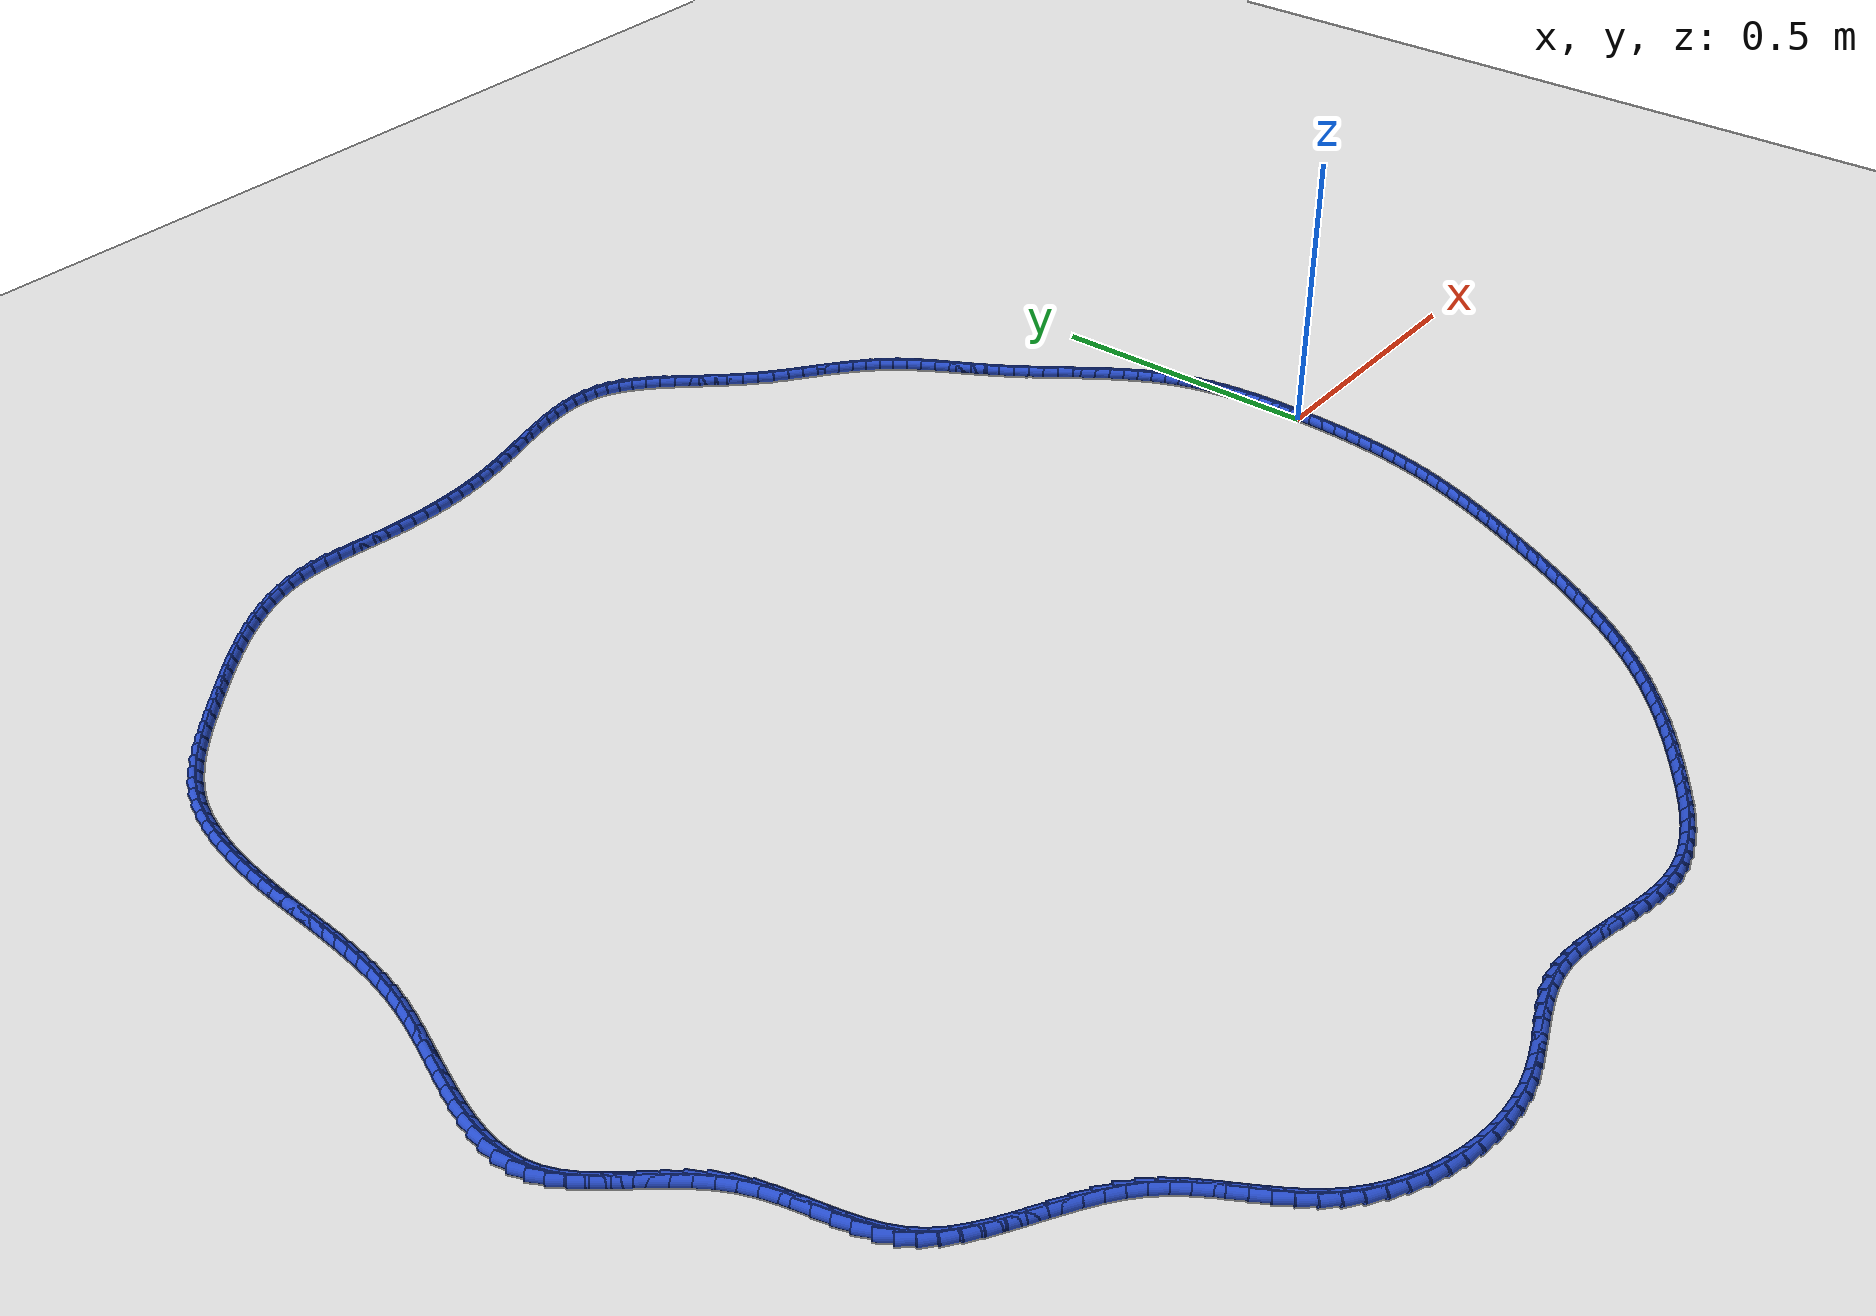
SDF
<sdf version="1.6">
 <world name="default">
  <light name="sun" type="directional">
   <pose>0 0 10 0 -0 0</pose>
   <diffuse>0.8 0.8 0.8 1</diffuse>
   <specular>0.2 0.2 0.2 1</specular>
   <attenuation>
    <range>1000</range>
    <constant>0.9</constant>
    <linear>0.01</linear>
    <quadratic>0.001</quadratic>
   </attenuation>
   <direction>-0.5 0.1 -0.9</direction>
  </light>
  <model name="ground_plane">
   <static>1</static>
   <link name="link">
    <collision name="collision">
     <geometry><plane><normal>0 0 1</normal><size>100 100</size></plane></geometry>
     <surface><friction><ode><mu>100</mu><mu2>50</mu2></ode></friction></surface>
    </collision>
    <visual name="visual">
     <cast_shadows>0</cast_shadows>
     <geometry><plane><normal>0 0 1</normal><size>100 100</size></plane></geometry>
     <material>
      <script><uri>file://media/materials/scripts/gazebo.material</uri><name>Gazebo/WhiteGlow</name></script>
     </material>
    </visual>
   </link>
  </model>
  <gravity>0 0 -9.8</gravity>
  <magnetic_field>6e-06 2.3e-05 -4.2e-05</magnetic_field>
  <atmosphere type="adiabatic"/>
  <physics name="default_physics" default="0" type="ode">
   <max_step_size>0.001</max_step_size>
   <real_time_factor>1</real_time_factor>
   <real_time_update_rate>1000</real_time_update_rate>
  </physics>
  <scene><ambient>0.4 0.4 0.4 1</ambient><background>0.7 0.7 0.7 1</background><shadows>1</shadows></scene>
  <spherical_coordinates>
   <surface_model>EARTH_WGS84</surface_model>
   <latitude_deg>0</latitude_deg>
   <longitude_deg>0</longitude_deg>
   <elevation>0</elevation>
   <heading_deg>0</heading_deg>
  </spherical_coordinates>
  <model name="line">
   <link name="link_0">
    <pose>6.288372600415926e-18 -5.551115123125783e-17 0.01 0 1.57 1.5576710177558442</pose>
    <collision name="collision">
     <geometry><cylinder><radius>0.01</radius><length>0.08</length></cylinder></geometry>
    </collision>
    <visual name="visual">
     <material>
      <script><name>Gazebo/Blue</name><uri>file://media/materials/scripts/gazebo.material</uri></script>
     </material>
     <geometry><cylinder><radius>0.01</radius><length>0.08</length></cylinder></geometry>
    </visual>
   </link>
   <link name="link_1">
    <pose>0.00035819239381342763 0.027288639335198456 0.01 0 1.57 -1.563014140440489</pose>
    <collision name="collision">
     <geometry><cylinder><radius>0.01</radius><length>0.08</length></cylinder></geometry>
    </collision>
    <visual name="visual">
     <material>
      <script><name>Gazebo/Blue</name><uri>file://media/materials/scripts/gazebo.material</uri></script>
     </material>
     <geometry><cylinder><radius>0.01</radius><length>0.08</length></cylinder></geometry>
    </visual>
   </link>
   <link name="link_2">
    <pose>0.0001455609213107466 0.05461093287966267 0.01 0 1.57 -1.5373915077967988</pose>
    <collision name="collision">
     <geometry><cylinder><radius>0.01</radius><length>0.08</length></cylinder></geometry>
    </collision>
    <visual name="visual">
     <material>
      <script><name>Gazebo/Blue</name><uri>file://media/materials/scripts/gazebo.material</uri></script>
     </material>
     <geometry><cylinder><radius>0.01</radius><length>0.08</length></cylinder></geometry>
    </visual>
   </link>
   <link name="link_3">
    <pose>-0.0007656347469176687 0.08187815783113758 0.01 0 1.57 -1.506824728913577</pose>
    <collision name="collision">
     <geometry><cylinder><radius>0.01</radius><length>0.08</length></cylinder></geometry>
    </collision>
    <visual name="visual">
     <material>
      <script><name>Gazebo/Blue</name><uri>file://media/materials/scripts/gazebo.material</uri></script>
     </material>
     <geometry><cylinder><radius>0.01</radius><length>0.08</length></cylinder></geometry>
    </visual>
   </link>
   <link name="link_4">
    <pose>-0.002503134940281458 0.10900159138736809 0.01 0 1.57 -1.4710373537824666</pose>
    <collision name="collision">
     <geometry><cylinder><radius>0.01</radius><length>0.08</length></cylinder></geometry>
    </collision>
    <visual name="visual">
     <material>
      <script><name>Gazebo/Blue</name><uri>file://media/materials/scripts/gazebo.material</uri></script>
     </material>
     <geometry><cylinder><radius>0.01</radius><length>0.08</length></cylinder></geometry>
    </visual>
   </link>
   <link name="link_5">
    <pose>-0.005194679988190256 0.13589251074609907 0.01 0 1.57 -1.42972331197012</pose>
    <collision name="collision">
     <geometry><cylinder><radius>0.01</radius><length>0.08</length></cylinder></geometry>
    </collision>
    <visual name="visual">
     <material>
      <script><name>Gazebo/Blue</name><uri>file://media/materials/scripts/gazebo.material</uri></script>
     </material>
     <geometry><cylinder><radius>0.01</radius><length>0.08</length></cylinder></geometry>
    </visual>
   </link>
   <link name="link_6">
    <pose>-0.008968010220053698 0.16246219310507543 0.01 0 1.57 -1.382572923634424</pose>
    <collision name="collision">
     <geometry><cylinder><radius>0.01</radius><length>0.08</length></cylinder></geometry>
    </collision>
    <visual name="visual">
     <material>
      <script><name>Gazebo/Blue</name><uri>file://media/materials/scripts/gazebo.material</uri></script>
     </material>
     <geometry><cylinder><radius>0.01</radius><length>0.08</length></cylinder></geometry>
    </visual>
   </link>
   <link name="link_7">
    <pose>-0.013950865965281417 0.18862191566204203 0.01 0 1.57 -1.329310111363557</pose>
    <collision name="collision">
     <geometry><cylinder><radius>0.01</radius><length>0.08</length></cylinder></geometry>
    </collision>
    <visual name="visual">
     <material>
      <script><name>Gazebo/Blue</name><uri>file://media/materials/scripts/gazebo.material</uri></script>
     </material>
     <geometry><cylinder><radius>0.01</radius><length>0.08</length></cylinder></geometry>
    </visual>
   </link>
   <link name="link_8">
    <pose>-0.020270987553283056 0.21428295561474392 0.01 0 1.57 -1.2697431346788266</pose>
    <collision name="collision">
     <geometry><cylinder><radius>0.01</radius><length>0.08</length></cylinder></geometry>
    </collision>
    <visual name="visual">
     <material>
      <script><name>Gazebo/Blue</name><uri>file://media/materials/scripts/gazebo.material</uri></script>
     </material>
     <geometry><cylinder><radius>0.01</radius><length>0.08</length></cylinder></geometry>
    </visual>
   </link>
   <link name="link_9">
    <pose>-0.028056115313468254 0.23935659016092592 0.01 0 1.57 -1.2043960556134092</pose>
    <collision name="collision">
     <geometry><cylinder><radius>0.01</radius><length>0.08</length></cylinder></geometry>
    </collision>
    <visual name="visual">
     <material>
      <script><name>Gazebo/Blue</name><uri>file://media/materials/scripts/gazebo.material</uri></script>
     </material>
     <geometry><cylinder><radius>0.01</radius><length>0.08</length></cylinder></geometry>
    </visual>
   </link>
   <link name="link_10">
    <pose>-0.03742097810335495 0.2637615625482717 0.01 0 1.57 -1.1413541810037235</pose>
    <collision name="collision">
     <geometry><cylinder><radius>0.01</radius><length>0.08</length></cylinder></geometry>
    </collision>
    <visual name="visual">
     <material>
      <script><name>Gazebo/Blue</name><uri>file://media/materials/scripts/gazebo.material</uri></script>
     </material>
     <geometry><cylinder><radius>0.01</radius><length>0.08</length></cylinder></geometry>
    </visual>
   </link>
   <link name="link_11">
    <pose>-0.048300866656210105 0.28751957854920734 0.01 0 1.57 -1.0868293325058338</pose>
    <collision name="collision">
     <geometry><cylinder><radius>0.01</radius><length>0.08</length></cylinder></geometry>
    </collision>
    <visual name="visual">
     <material>
      <script><name>Gazebo/Blue</name><uri>file://media/materials/scripts/gazebo.material</uri></script>
     </material>
     <geometry><cylinder><radius>0.01</radius><length>0.08</length></cylinder></geometry>
    </visual>
   </link>
   <link name="link_12">
    <pose>-0.06050034722363524 0.3107273543205694 0.01 0 1.57 -1.0412027712834304</pose>
    <collision name="collision">
     <geometry><cylinder><radius>0.01</radius><length>0.08</length></cylinder></geometry>
    </collision>
    <visual name="visual">
     <material>
      <script><name>Gazebo/Blue</name><uri>file://media/materials/scripts/gazebo.material</uri></script>
     </material>
     <geometry><cylinder><radius>0.01</radius><length>0.08</length></cylinder></geometry>
    </visual>
   </link>
   <link name="link_13">
    <pose>-0.07382102474752579 0.33348330523403574 0.01 0 1.57 -1.0044701815467032</pose>
    <collision name="collision">
     <geometry><cylinder><radius>0.01</radius><length>0.08</length></cylinder></geometry>
    </collision>
    <visual name="visual">
     <material>
      <script><name>Gazebo/Blue</name><uri>file://media/materials/scripts/gazebo.material</uri></script>
     </material>
     <geometry><cylinder><radius>0.01</radius><length>0.08</length></cylinder></geometry>
    </visual>
   </link>
   <link name="link_14">
    <pose>-0.08806450416977718 0.3558858466612842 0.01 0 1.57 -0.9764794870385074</pose>
    <collision name="collision">
     <geometry><cylinder><radius>0.01</radius><length>0.08</length></cylinder></geometry>
    </collision>
    <visual name="visual">
     <material>
      <script><name>Gazebo/Blue</name><uri>file://media/materials/scripts/gazebo.material</uri></script>
     </material>
     <geometry><cylinder><radius>0.01</radius><length>0.08</length></cylinder></geometry>
    </visual>
   </link>
   <link name="link_15">
    <pose>-0.10303239043228493 0.37803339397399294 0.01 0 1.57 -0.9570182973954346</pose>
    <collision name="collision">
     <geometry><cylinder><radius>0.01</radius><length>0.08</length></cylinder></geometry>
    </collision>
    <visual name="visual">
     <material>
      <script><name>Gazebo/Blue</name><uri>file://media/materials/scripts/gazebo.material</uri></script>
     </material>
     <geometry><cylinder><radius>0.01</radius><length>0.08</length></cylinder></geometry>
    </visual>
   </link>
   <link name="link_16">
    <pose>-0.11852628847694446 0.40002436254384 0.01 0 1.57 -0.9458761800640695</pose>
    <collision name="collision">
     <geometry><cylinder><radius>0.01</radius><length>0.08</length></cylinder></geometry>
    </collision>
    <visual name="visual">
     <material>
      <script><name>Gazebo/Blue</name><uri>file://media/materials/scripts/gazebo.material</uri></script>
     </material>
     <geometry><cylinder><radius>0.01</radius><length>0.08</length></cylinder></geometry>
    </visual>
   </link>
   <link name="link_17">
    <pose>-0.1343478032456513 0.4219571677425031 0.01 0 1.57 -0.9428837347033211</pose>
    <collision name="collision">
     <geometry><cylinder><radius>0.01</radius><length>0.08</length></cylinder></geometry>
    </collision>
    <visual name="visual">
     <material>
      <script><name>Gazebo/Blue</name><uri>file://media/materials/scripts/gazebo.material</uri></script>
     </material>
     <geometry><cylinder><radius>0.01</radius><length>0.08</length></cylinder></geometry>
    </visual>
   </link>
   <link name="link_18">
    <pose>-0.1502985396803008 0.4439302249416603 0.01 0 1.57 -0.9479322230216088</pose>
    <collision name="collision">
     <geometry><cylinder><radius>0.01</radius><length>0.08</length></cylinder></geometry>
    </collision>
    <visual name="visual">
     <material>
      <script><name>Gazebo/Blue</name><uri>file://media/materials/scripts/gazebo.material</uri></script>
     </material>
     <geometry><cylinder><radius>0.01</radius><length>0.08</length></cylinder></geometry>
    </visual>
   </link>
   <link name="link_19">
    <pose>-0.1661801027227884 0.46604194951298944 0.01 0 1.57 -0.9609769665578496</pose>
    <collision name="collision">
     <geometry><cylinder><radius>0.01</radius><length>0.08</length></cylinder></geometry>
    </collision>
    <visual name="visual">
     <material>
      <script><name>Gazebo/Blue</name><uri>file://media/materials/scripts/gazebo.material</uri></script>
     </material>
     <geometry><cylinder><radius>0.01</radius><length>0.08</length></cylinder></geometry>
    </visual>
   </link>
   <link name="link_20">
    <pose>-0.18179409731500973 0.4883907568281688 0.01 0 1.57 -0.9820262279820207</pose>
    <collision name="collision">
     <geometry><cylinder><radius>0.01</radius><length>0.08</length></cylinder></geometry>
    </collision>
    <visual name="visual">
     <material>
      <script><name>Gazebo/Blue</name><uri>file://media/materials/scripts/gazebo.material</uri></script>
     </material>
     <geometry><cylinder><radius>0.01</radius><length>0.08</length></cylinder></geometry>
    </visual>
   </link>
   <link name="link_21">
    <pose>-0.19694212839886005 0.5110750622588759 0.01 0 1.57 -1.0109300378586217</pose>
    <collision name="collision">
     <geometry><cylinder><radius>0.01</radius><length>0.08</length></cylinder></geometry>
    </collision>
    <visual name="visual">
     <material>
      <script><name>Gazebo/Blue</name><uri>file://media/materials/scripts/gazebo.material</uri></script>
     </material>
     <geometry><cylinder><radius>0.01</radius><length>0.08</length></cylinder></geometry>
    </visual>
   </link>
   <link name="link_22">
    <pose>-0.2114299420428363 0.5341903500423052 0.01 0 1.57 -1.039145391755223</pose>
    <collision name="collision">
     <geometry><cylinder><radius>0.01</radius><length>0.08</length></cylinder></geometry>
    </collision>
    <visual name="visual">
     <material>
      <script><name>Gazebo/Blue</name><uri>file://media/materials/scripts/gazebo.material</uri></script>
     </material>
     <geometry><cylinder><radius>0.01</radius><length>0.08</length></cylinder></geometry>
    </visual>
   </link>
   <link name="link_23">
    <pose>-0.22525480229039502 0.5576965459083251 0.01 0 1.57 -1.0547436627425568</pose>
    <collision name="collision">
     <geometry><cylinder><radius>0.01</radius><length>0.08</length></cylinder></geometry>
    </collision>
    <visual name="visual">
     <material>
      <script><name>Gazebo/Blue</name><uri>file://media/materials/scripts/gazebo.material</uri></script>
     </material>
     <geometry><cylinder><radius>0.01</radius><length>0.08</length></cylinder></geometry>
    </visual>
   </link>
   <link name="link_24">
    <pose>-0.23868202464836102 0.581363845843327 0.01 0 1.57 -1.056841591952224</pose>
    <collision name="collision">
     <geometry><cylinder><radius>0.01</radius><length>0.08</length></cylinder></geometry>
    </collision>
    <visual name="visual">
     <material>
      <script><name>Gazebo/Blue</name><uri>file://media/materials/scripts/gazebo.material</uri></script>
     </material>
     <geometry><cylinder><radius>0.01</radius><length>0.08</length></cylinder></geometry>
    </visual>
   </link>
   <link name="link_25">
    <pose>-0.25199691686086373 0.604948295110525 0.01 0 1.57 -1.0452628420765173</pose>
    <collision name="collision">
     <geometry><cylinder><radius>0.01</radius><length>0.08</length></cylinder></geometry>
    </collision>
    <visual name="visual">
     <material>
      <script><name>Gazebo/Blue</name><uri>file://media/materials/scripts/gazebo.material</uri></script>
     </material>
     <geometry><cylinder><radius>0.01</radius><length>0.08</length></cylinder></geometry>
    </visual>
   </link>
   <link name="link_26">
    <pose>-0.2654847866720326 0.6282059389731328 0.01 0 1.57 -1.0196211803375106</pose>
    <collision name="collision">
     <geometry><cylinder><radius>0.01</radius><length>0.08</length></cylinder></geometry>
    </collision>
    <visual name="visual">
     <material>
      <script><name>Gazebo/Blue</name><uri>file://media/materials/scripts/gazebo.material</uri></script>
     </material>
     <geometry><cylinder><radius>0.01</radius><length>0.08</length></cylinder></geometry>
    </visual>
   </link>
   <link name="link_27">
    <pose>-0.2794309418259971 0.6508928226943647 0.01 0 1.57 -0.9793735186141798</pose>
    <collision name="collision">
     <geometry><cylinder><radius>0.01</radius><length>0.08</length></cylinder></geometry>
    </collision>
    <visual name="visual">
     <material>
      <script><name>Gazebo/Blue</name><uri>file://media/materials/scripts/gazebo.material</uri></script>
     </material>
     <geometry><cylinder><radius>0.01</radius><length>0.08</length></cylinder></geometry>
    </visual>
   </link>
   <link name="link_28">
    <pose>-0.2941206900668865 0.6727649915374343 0.01 0 1.57 -0.9239665071199855</pose>
    <collision name="collision">
     <geometry><cylinder><radius>0.01</radius><length>0.08</length></cylinder></geometry>
    </collision>
    <visual name="visual">
     <material>
      <script><name>Gazebo/Blue</name><uri>file://media/materials/scripts/gazebo.material</uri></script>
     </material>
     <geometry><cylinder><radius>0.01</radius><length>0.08</length></cylinder></geometry>
    </visual>
   </link>
   <link name="link_29">
    <pose>-0.3098393391388304 0.6935784907655561 0.01 0 1.57 -0.8539680803957829</pose>
    <collision name="collision">
     <geometry><cylinder><radius>0.01</radius><length>0.08</length></cylinder></geometry>
    </collision>
    <visual name="visual">
     <material>
      <script><name>Gazebo/Blue</name><uri>file://media/materials/scripts/gazebo.material</uri></script>
     </material>
     <geometry><cylinder><radius>0.01</radius><length>0.08</length></cylinder></geometry>
    </visual>
   </link>
   <link name="link_30">
    <pose>-0.3268565889247437 0.7131055129945613 0.01 0 1.57 -0.7843573897227736</pose>
    <collision name="collision">
     <geometry><cylinder><radius>0.01</radius><length>0.08</length></cylinder></geometry>
    </collision>
    <visual name="visual">
     <material>
      <script><name>Gazebo/Blue</name><uri>file://media/materials/scripts/gazebo.material</uri></script>
     </material>
     <geometry><cylinder><radius>0.01</radius><length>0.08</length></cylinder></geometry>
    </visual>
   </link>
   <link name="link_31">
    <pose>-0.3451793251737625 0.7313901492402318 0.01 0 1.57 -0.7281658685395936</pose>
    <collision name="collision">
     <geometry><cylinder><radius>0.01</radius><length>0.08</length></cylinder></geometry>
    </collision>
    <visual name="visual">
     <material>
      <script><name>Gazebo/Blue</name><uri>file://media/materials/scripts/gazebo.material</uri></script>
     </material>
     <geometry><cylinder><radius>0.01</radius><length>0.08</length></cylinder></geometry>
    </visual>
   </link>
   <link name="link_32">
    <pose>-0.3645960164219315 0.7487024574018947 0.01 0 1.57 -0.6861414759151395</pose>
    <collision name="collision">
     <geometry><cylinder><radius>0.01</radius><length>0.08</length></cylinder></geometry>
    </collision>
    <visual name="visual">
     <material>
      <script><name>Gazebo/Blue</name><uri>file://media/materials/scripts/gazebo.material</uri></script>
     </material>
     <geometry><cylinder><radius>0.01</radius><length>0.08</length></cylinder></geometry>
    </visual>
   </link>
   <link name="link_33">
    <pose>-0.3848884981430086 0.7653193577153742 0.01 0 1.57 -0.6581782373925901</pose>
    <collision name="collision">
     <geometry><cylinder><radius>0.01</radius><length>0.08</length></cylinder></geometry>
    </collision>
    <visual name="visual">
     <material>
      <script><name>Gazebo/Blue</name><uri>file://media/materials/scripts/gazebo.material</uri></script>
     </material>
     <geometry><cylinder><radius>0.01</radius><length>0.08</length></cylinder></geometry>
    </visual>
   </link>
   <link name="link_34">
    <pose>-0.40583860581075154 0.7815177704164963 0.01 0 1.57 -0.643939862634523</pose>
    <collision name="collision">
     <geometry><cylinder><radius>0.01</radius><length>0.08</length></cylinder></geometry>
    </collision>
    <visual name="visual">
     <material>
      <script><name>Gazebo/Blue</name><uri>file://media/materials/scripts/gazebo.material</uri></script>
     </material>
     <geometry><cylinder><radius>0.01</radius><length>0.08</length></cylinder></geometry>
    </visual>
   </link>
   <link name="link_35">
    <pose>-0.42722817489891823 0.7975746157410857 0.01 0 1.57 -0.6430285478457716</pose>
    <collision name="collision">
     <geometry><cylinder><radius>0.01</radius><length>0.08</length></cylinder></geometry>
    </collision>
    <visual name="visual">
     <material>
      <script><name>Gazebo/Blue</name><uri>file://media/materials/scripts/gazebo.material</uri></script>
     </material>
     <geometry><cylinder><radius>0.01</radius><length>0.08</length></cylinder></geometry>
    </visual>
   </link>
   <link name="link_36">
    <pose>-0.4488390408812666 0.8137668139249673 0.01 0 1.57 -0.6550651116794389</pose>
    <collision name="collision">
     <geometry><cylinder><radius>0.01</radius><length>0.08</length></cylinder></geometry>
    </collision>
    <visual name="visual">
     <material>
      <script><name>Gazebo/Blue</name><uri>file://media/materials/scripts/gazebo.material</uri></script>
     </material>
     <geometry><cylinder><radius>0.01</radius><length>0.08</length></cylinder></geometry>
    </visual>
   </link>
   <link name="link_37">
    <pose>-0.4704530392315542 0.8303712852039663 0.01 0 1.57 -0.6796932818834382</pose>
    <collision name="collision">
     <geometry><cylinder><radius>0.01</radius><length>0.08</length></cylinder></geometry>
    </collision>
    <visual name="visual">
     <material>
      <script><name>Gazebo/Blue</name><uri>file://media/materials/scripts/gazebo.material</uri></script>
     </material>
     <geometry><cylinder><radius>0.01</radius><length>0.08</length></cylinder></geometry>
    </visual>
   </link>
   <link name="link_38">
    <pose>-0.4918520054235393 0.847664949813908 0.01 0 1.57 -0.7165218541864354</pose>
    <collision name="collision">
     <geometry><cylinder><radius>0.01</radius><length>0.08</length></cylinder></geometry>
    </collision>
    <visual name="visual">
     <material>
      <script><name>Gazebo/Blue</name><uri>file://media/materials/scripts/gazebo.material</uri></script>
     </material>
     <geometry><cylinder><radius>0.01</radius><length>0.08</length></cylinder></geometry>
    </visual>
   </link>
   <link name="link_39">
    <pose>-0.5128177749309796 0.8659247279906175 0.01 0 1.57 -0.7637926570264485</pose>
    <collision name="collision">
     <geometry><cylinder><radius>0.01</radius><length>0.08</length></cylinder></geometry>
    </collision>
    <visual name="visual">
     <material>
      <script><name>Gazebo/Blue</name><uri>file://media/materials/scripts/gazebo.material</uri></script>
     </material>
     <geometry><cylinder><radius>0.01</radius><length>0.08</length></cylinder></geometry>
    </visual>
   </link>
   <link name="link_40">
    <pose>-0.5331489305177755 0.8853958024112147 0.01 0 1.57 -0.8047659717073926</pose>
    <collision name="collision">
     <geometry><cylinder><radius>0.01</radius><length>0.08</length></cylinder></geometry>
    </collision>
    <visual name="visual">
     <material>
      <script><name>Gazebo/Blue</name><uri>file://media/materials/scripts/gazebo.material</uri></script>
     </material>
     <geometry><cylinder><radius>0.01</radius><length>0.08</length></cylinder></geometry>
    </visual>
   </link>
   <link name="link_41">
    <pose>-0.552869728734417 0.9058956844705387 0.01 0 1.57 -0.8285849994221972</pose>
    <collision name="collision">
     <geometry><cylinder><radius>0.01</radius><length>0.08</length></cylinder></geometry>
    </collision>
    <visual name="visual">
     <material>
      <script><name>Gazebo/Blue</name><uri>file://media/materials/scripts/gazebo.material</uri></script>
     </material>
     <geometry><cylinder><radius>0.01</radius><length>0.08</length></cylinder></geometry>
    </visual>
   </link>
   <link name="link_42">
    <pose>-0.5721662287740646 0.9269352556055884 0.01 0 1.57 -0.8357144583643168</pose>
    <collision name="collision">
     <geometry><cylinder><radius>0.01</radius><length>0.08</length></cylinder></geometry>
    </collision>
    <visual name="visual">
     <material>
      <script><name>Gazebo/Blue</name><uri>file://media/materials/scripts/gazebo.material</uri></script>
     </material>
     <geometry><cylinder><radius>0.01</radius><length>0.08</length></cylinder></geometry>
    </visual>
   </link>
   <link name="link_43">
    <pose>-0.5912280179543508 0.9480187111533087 0.01 0 1.57 -0.8261056235948407</pose>
    <collision name="collision">
     <geometry><cylinder><radius>0.01</radius><length>0.08</length></cylinder></geometry>
    </collision>
    <visual name="visual">
     <material>
      <script><name>Gazebo/Blue</name><uri>file://media/materials/scripts/gazebo.material</uri></script>
     </material>
     <geometry><cylinder><radius>0.01</radius><length>0.08</length></cylinder></geometry>
    </visual>
   </link>
   <link name="link_44">
    <pose>-0.6102446835929072 0.9686502464506442 0.01 0 1.57 -0.7988529256225197</pose>
    <collision name="collision">
     <geometry><cylinder><radius>0.01</radius><length>0.08</length></cylinder></geometry>
    </collision>
    <visual name="visual">
     <material>
      <script><name>Gazebo/Blue</name><uri>file://media/materials/scripts/gazebo.material</uri></script>
     </material>
     <geometry><cylinder><radius>0.01</radius><length>0.08</length></cylinder></geometry>
    </visual>
   </link>
   <link name="link_45">
    <pose>-0.6294058130073666 0.9883340568345396 0.01 0 1.57 -0.7521552305515299</pose>
    <collision name="collision">
     <geometry><cylinder><radius>0.01</radius><length>0.08</length></cylinder></geometry>
    </collision>
    <visual name="visual">
     <material>
      <script><name>Gazebo/Blue</name><uri>file://media/materials/scripts/gazebo.material</uri></script>
     </material>
     <geometry><cylinder><radius>0.01</radius><length>0.08</length></cylinder></geometry>
    </visual>
   </link>
   <link name="link_46">
    <pose>-0.6489009935153609 1.0065743376419392 0.01 0 1.57 -0.6833884912621196</pose>
    <collision name="collision">
     <geometry><cylinder><radius>0.01</radius><length>0.08</length></cylinder></geometry>
    </collision>
    <visual name="visual">
     <material>
      <script><name>Gazebo/Blue</name><uri>file://media/materials/scripts/gazebo.material</uri></script>
     </material>
     <geometry><cylinder><radius>0.01</radius><length>0.08</length></cylinder></geometry>
    </visual>
   </link>
   <link name="link_47">
    <pose>-0.6689198124345221 1.0228752842097881 0.01 0 1.57 -0.5894852782856621</pose>
    <collision name="collision">
     <geometry><cylinder><radius>0.01</radius><length>0.08</length></cylinder></geometry>
    </collision>
    <visual name="visual">
     <material>
      <script><name>Gazebo/Blue</name><uri>file://media/materials/scripts/gazebo.material</uri></script>
     </material>
     <geometry><cylinder><radius>0.01</radius><length>0.08</length></cylinder></geometry>
    </visual>
   </link>
   <link name="link_48">
    <pose>-0.689651857082483 1.0367410918750308 0.01 0 1.57 -0.4679806199214394</pose>
    <collision name="collision">
     <geometry><cylinder><radius>0.01</radius><length>0.08</length></cylinder></geometry>
    </collision>
    <visual name="visual">
     <material>
      <script><name>Gazebo/Blue</name><uri>file://media/materials/scripts/gazebo.material</uri></script>
     </material>
     <geometry><cylinder><radius>0.01</radius><length>0.08</length></cylinder></geometry>
    </visual>
   </link>
   <link name="link_49">
    <pose>-0.7112867147768751 1.0476759559746118 0.01 0 1.57 -0.3211746160896842</pose>
    <collision name="collision">
     <geometry><cylinder><radius>0.01</radius><length>0.08</length></cylinder></geometry>
    </collision>
    <visual name="visual">
     <material>
      <script><name>Gazebo/Blue</name><uri>file://media/materials/scripts/gazebo.material</uri></script>
     </material>
     <geometry><cylinder><radius>0.01</radius><length>0.08</length></cylinder></geometry>
    </visual>
   </link>
   <link name="link_50">
    <pose>-0.7339974164544913 1.0552316593627975 0.01 0 1.57 -0.17690437842264709</pose>
    <collision name="collision">
     <geometry><cylinder><radius>0.01</radius><length>0.08</length></cylinder></geometry>
    </collision>
    <visual name="visual">
     <material>
      <script><name>Gazebo/Blue</name><uri>file://media/materials/scripts/gazebo.material</uri></script>
     </material>
     <geometry><cylinder><radius>0.01</radius><length>0.08</length></cylinder></geometry>
    </visual>
   </link>
   <link name="link_51">
    <pose>-0.7577752057844984 1.059482490677623 0.01 0 1.57 -0.054279942633761936</pose>
    <collision name="collision">
     <geometry><cylinder><radius>0.01</radius><length>0.08</length></cylinder></geometry>
    </collision>
    <visual name="visual">
     <material>
      <script><name>Gazebo/Blue</name><uri>file://media/materials/scripts/gazebo.material</uri></script>
     </material>
     <geometry><cylinder><radius>0.01</radius><length>0.08</length></cylinder></geometry>
    </visual>
   </link>
   <link name="link_52">
    <pose>-0.7824989244576854 1.0608258122496703 0.01 0 1.57 0.04545525336521164</pose>
    <collision name="collision">
     <geometry><cylinder><radius>0.01</radius><length>0.08</length></cylinder></geometry>
    </collision>
    <visual name="visual">
     <material>
      <script><name>Gazebo/Blue</name><uri>file://media/materials/scripts/gazebo.material</uri></script>
     </material>
     <geometry><cylinder><radius>0.01</radius><length>0.08</length></cylinder></geometry>
    </visual>
   </link>
   <link name="link_53">
    <pose>-0.8080457483329381 1.059663774461046 0.01 0 1.57 0.12376819300810715</pose>
    <collision name="collision">
     <geometry><cylinder><radius>0.01</radius><length>0.08</length></cylinder></geometry>
    </collision>
    <visual name="visual">
     <material>
      <script><name>Gazebo/Blue</name><uri>file://media/materials/scripts/gazebo.material</uri></script>
     </material>
     <geometry><cylinder><radius>0.01</radius><length>0.08</length></cylinder></geometry>
    </visual>
   </link>
   <link name="link_54">
    <pose>-0.8342928532691425 1.056398527693856 0.01 0 1.57 0.1830673455067763</pose>
    <collision name="collision">
     <geometry><cylinder><radius>0.01</radius><length>0.08</length></cylinder></geometry>
    </collision>
    <visual name="visual">
     <material>
      <script><name>Gazebo/Blue</name><uri>file://media/materials/scripts/gazebo.material</uri></script>
     </material>
     <geometry><cylinder><radius>0.01</radius><length>0.08</length></cylinder></geometry>
    </visual>
   </link>
   <link name="link_55">
    <pose>-0.8611174151251849 1.0514322223302068 0.01 0 1.57 0.22575497828030935</pose>
    <collision name="collision">
     <geometry><cylinder><radius>0.01</radius><length>0.08</length></cylinder></geometry>
    </collision>
    <visual name="visual">
     <material>
      <script><name>Gazebo/Blue</name><uri>file://media/materials/scripts/gazebo.material</uri></script>
     </material>
     <geometry><cylinder><radius>0.01</radius><length>0.08</length></cylinder></geometry>
    </visual>
   </link>
   <link name="link_56">
    <pose>-0.8883966097599513 1.0451670087522047 0.01 0 1.57 0.25379501297461127</pose>
    <collision name="collision">
     <geometry><cylinder><radius>0.01</radius><length>0.08</length></cylinder></geometry>
    </collision>
    <visual name="visual">
     <material>
      <script><name>Gazebo/Blue</name><uri>file://media/materials/scripts/gazebo.material</uri></script>
     </material>
     <geometry><cylinder><radius>0.01</radius><length>0.08</length></cylinder></geometry>
    </visual>
   </link>
   <link name="link_57">
    <pose>-0.9160076130323278 1.0380050373419563 0.01 0 1.57 0.26856945610888344</pose>
    <collision name="collision">
     <geometry><cylinder><radius>0.01</radius><length>0.08</length></cylinder></geometry>
    </collision>
    <visual name="visual">
     <material>
      <script><name>Gazebo/Blue</name><uri>file://media/materials/scripts/gazebo.material</uri></script>
     </material>
     <geometry><cylinder><radius>0.01</radius><length>0.08</length></cylinder></geometry>
    </visual>
   </link>
   <link name="link_58">
    <pose>-0.9438276008012003 1.0303484584815674 0.01 0 1.57 0.27085796134496737</pose>
    <collision name="collision">
     <geometry><cylinder><radius>0.01</radius><length>0.08</length></cylinder></geometry>
    </collision>
    <visual name="visual">
     <material>
      <script><name>Gazebo/Blue</name><uri>file://media/materials/scripts/gazebo.material</uri></script>
     </material>
     <geometry><cylinder><radius>0.01</radius><length>0.08</length></cylinder></geometry>
    </visual>
   </link>
   <link name="link_59">
    <pose>-0.9717337489254549 1.022599422553145 0.01 0 1.57 0.260852954387198</pose>
    <collision name="collision">
     <geometry><cylinder><radius>0.01</radius><length>0.08</length></cylinder></geometry>
    </collision>
    <visual name="visual">
     <material>
      <script><name>Gazebo/Blue</name><uri>file://media/materials/scripts/gazebo.material</uri></script>
     </material>
     <geometry><cylinder><radius>0.01</radius><length>0.08</length></cylinder></geometry>
    </visual>
   </link>
   <link name="link_60">
    <pose>-0.9996032332639778 1.0151600799387952 0.01 0 1.57 0.23817415935696407</pose>
    <collision name="collision">
     <geometry><cylinder><radius>0.01</radius><length>0.08</length></cylinder></geometry>
    </collision>
    <visual name="visual">
     <material>
      <script><name>Gazebo/Blue</name><uri>file://media/materials/scripts/gazebo.material</uri></script>
     </material>
     <geometry><cylinder><radius>0.01</radius><length>0.08</length></cylinder></geometry>
    </visual>
   </link>
   <link name="link_61">
    <pose>-1.0273132296756553 1.0084325810206245 0.01 0 1.57 0.20265592370087682</pose>
    <collision name="collision">
     <geometry><cylinder><radius>0.01</radius><length>0.08</length></cylinder></geometry>
    </collision>
    <visual name="visual">
     <material>
      <script><name>Gazebo/Blue</name><uri>file://media/materials/scripts/gazebo.material</uri></script>
     </material>
     <geometry><cylinder><radius>0.01</radius><length>0.08</length></cylinder></geometry>
    </visual>
   </link>
   <link name="link_62">
    <pose>-1.0547498974900416 1.0027949880581728 0.01 0 1.57 0.1620402487110609</pose>
    <collision name="collision">
     <geometry><cylinder><radius>0.01</radius><length>0.08</length></cylinder></geometry>
    </collision>
    <visual name="visual">
     <material>
      <script><name>Gazebo/Blue</name><uri>file://media/materials/scripts/gazebo.material</uri></script>
     </material>
     <geometry><cylinder><radius>0.01</radius><length>0.08</length></cylinder></geometry>
    </visual>
   </link>
   <link name="link_63">
    <pose>-1.081899579336812 0.9983567335462266 0.01 0 1.57 0.12192371084893064</pose>
    <collision name="collision">
     <geometry><cylinder><radius>0.01</radius><length>0.08</length></cylinder></geometry>
    </collision>
    <visual name="visual">
     <material>
      <script><name>Gazebo/Blue</name><uri>file://media/materials/scripts/gazebo.material</uri></script>
     </material>
     <geometry><cylinder><radius>0.01</radius><length>0.08</length></cylinder></geometry>
    </visual>
   </link>
   <link name="link_64">
    <pose>-1.1088112899800755 0.9950592020044183 0.01 0 1.57 0.08280756498412006</pose>
    <collision name="collision">
     <geometry><cylinder><radius>0.01</radius><length>0.08</length></cylinder></geometry>
    </collision>
    <visual name="visual">
     <material>
      <script><name>Gazebo/Blue</name><uri>file://media/materials/scripts/gazebo.material</uri></script>
     </material>
     <geometry><cylinder><radius>0.01</radius><length>0.08</length></cylinder></geometry>
    </visual>
   </link>
   <link name="link_65">
    <pose>-1.13553500399622 0.9928412043283688 0.01 0 1.57 0.045093416216564264</pose>
    <collision name="collision">
     <geometry><cylinder><radius>0.01</radius><length>0.08</length></cylinder></geometry>
    </collision>
    <visual name="visual">
     <material>
      <script><name>Gazebo/Blue</name><uri>file://media/materials/scripts/gazebo.material</uri></script>
     </material>
     <geometry><cylinder><radius>0.01</radius><length>0.08</length></cylinder></geometry>
    </visual>
   </link>
   <link name="link_66">
    <pose>-1.1621206959616333 0.9916415514136986 0.01 0 1.57 0.009151397897049707</pose>
    <collision name="collision">
     <geometry><cylinder><radius>0.01</radius><length>0.08</length></cylinder></geometry>
    </collision>
    <visual name="visual">
     <material>
      <script><name>Gazebo/Blue</name><uri>file://media/materials/scripts/gazebo.material</uri></script>
     </material>
     <geometry><cylinder><radius>0.01</radius><length>0.08</length></cylinder></geometry>
    </visual>
   </link>
   <link name="link_67">
    <pose>-1.1886183404527033 0.9913990541560282 0.01 0 1.57 -0.02469187692447737</pose>
    <collision name="collision">
     <geometry><cylinder><radius>0.01</radius><length>0.08</length></cylinder></geometry>
    </collision>
    <visual name="visual">
     <material>
      <script><name>Gazebo/Blue</name><uri>file://media/materials/scripts/gazebo.material</uri></script>
     </material>
     <geometry><cylinder><radius>0.01</radius><length>0.08</length></cylinder></geometry>
    </visual>
   </link>
   <link name="link_68">
    <pose>-1.2150779120458184 0.9920525234509785 0.01 0 1.57 -0.0561616533493815</pose>
    <collision name="collision">
     <geometry><cylinder><radius>0.01</radius><length>0.08</length></cylinder></geometry>
    </collision>
    <visual name="visual">
     <material>
      <script><name>Gazebo/Blue</name><uri>file://media/materials/scripts/gazebo.material</uri></script>
     </material>
     <geometry><cylinder><radius>0.01</radius><length>0.08</length></cylinder></geometry>
    </visual>
   </link>
   <link name="link_69">
    <pose>-1.2415493853173654 0.9935407701941695 0.01 0 1.57 -0.08503940108665022</pose>
    <collision name="collision">
     <geometry><cylinder><radius>0.01</radius><length>0.08</length></cylinder></geometry>
    </collision>
    <visual name="visual">
     <material>
      <script><name>Gazebo/Blue</name><uri>file://media/materials/scripts/gazebo.material</uri></script>
     </material>
     <geometry><cylinder><radius>0.01</radius><length>0.08</length></cylinder></geometry>
    </visual>
   </link>
   <link name="link_70">
    <pose>-1.268082734843734 0.995802605281223 0.01 0 1.57 -0.11116347393558543</pose>
    <collision name="collision">
     <geometry><cylinder><radius>0.01</radius><length>0.08</length></cylinder></geometry>
    </collision>
    <visual name="visual">
     <material>
      <script><name>Gazebo/Blue</name><uri>file://media/materials/scripts/gazebo.material</uri></script>
     </material>
     <geometry><cylinder><radius>0.01</radius><length>0.08</length></cylinder></geometry>
    </visual>
   </link>
   <link name="link_71">
    <pose>-1.2947279352013108 0.9987768396077585 0.01 0 1.57 -0.1317621910871081</pose>
    <collision name="collision">
     <geometry><cylinder><radius>0.01</radius><length>0.08</length></cylinder></geometry>
    </collision>
    <visual name="visual">
     <material>
      <script><name>Gazebo/Blue</name><uri>file://media/materials/scripts/gazebo.material</uri></script>
     </material>
     <geometry><cylinder><radius>0.01</radius><length>0.08</length></cylinder></geometry>
    </visual>
   </link>
   <link name="link_72">
    <pose>-1.3215118629424776 1.0023265147235456 0.01 0 1.57 -0.13445268535226676</pose>
    <collision name="collision">
     <geometry><cylinder><radius>0.01</radius><length>0.08</length></cylinder></geometry>
    </collision>
    <visual name="visual">
     <material>
      <script><name>Gazebo/Blue</name><uri>file://media/materials/scripts/gazebo.material</uri></script>
     </material>
     <geometry><cylinder><radius>0.01</radius><length>0.08</length></cylinder></geometry>
    </visual>
   </link>
   <link name="link_73">
    <pose>-1.3483524217706022 1.0059572043065252 0.01 0 1.57 -0.11567290773619718</pose>
    <collision name="collision">
     <geometry><cylinder><radius>0.01</radius><length>0.08</length></cylinder></geometry>
    </collision>
    <visual name="visual">
     <material>
      <script><name>Gazebo/Blue</name><uri>file://media/materials/scripts/gazebo.material</uri></script>
     </material>
     <geometry><cylinder><radius>0.01</radius><length>0.08</length></cylinder></geometry>
    </visual>
   </link>
   <link name="link_74">
    <pose>-1.3751354090244534 1.0090691622790233 0.01 0 1.57 -0.07477108986260889</pose>
    <collision name="collision">
     <geometry><cylinder><radius>0.01</radius><length>0.08</length></cylinder></geometry>
    </collision>
    <visual name="visual">
     <material>
      <script><name>Gazebo/Blue</name><uri>file://media/materials/scripts/gazebo.material</uri></script>
     </material>
     <geometry><cylinder><radius>0.01</radius><length>0.08</length></cylinder></geometry>
    </visual>
   </link>
   <link name="link_75">
    <pose>-1.4017466175091873 1.0110626276915926 0.01 0 1.57 -0.010453924081235516</pose>
    <collision name="collision">
     <geometry><cylinder><radius>0.01</radius><length>0.08</length></cylinder></geometry>
    </collision>
    <visual name="visual">
     <material>
      <script><name>Gazebo/Blue</name><uri>file://media/materials/scripts/gazebo.material</uri></script>
     </material>
     <geometry><cylinder><radius>0.01</radius><length>0.08</length></cylinder></geometry>
    </visual>
   </link>
   <link name="link_76">
    <pose>-1.4280718400299628 1.0113378395947872 0.01 0 1.57 0.07715570996890839</pose>
    <collision name="collision">
     <geometry><cylinder><radius>0.01</radius><length>0.08</length></cylinder></geometry>
    </collision>
    <visual name="visual">
     <material>
      <script><name>Gazebo/Blue</name><uri>file://media/materials/scripts/gazebo.material</uri></script>
     </material>
     <geometry><cylinder><radius>0.01</radius><length>0.08</length></cylinder></geometry>
    </visual>
   </link>
   <link name="link_77">
    <pose>-1.454003141399063 1.0093331119973958 0.01 0 1.57 0.17054202265992902</pose>
    <collision name="collision">
     <geometry><cylinder><radius>0.01</radius><length>0.08</length></cylinder></geometry>
    </collision>
    <visual name="visual">
     <material>
      <script><name>Gazebo/Blue</name><uri>file://media/materials/scripts/gazebo.material</uri></script>
     </material>
     <geometry><cylinder><radius>0.01</radius><length>0.08</length></cylinder></geometry>
    </visual>
   </link>
   <link name="link_78">
    <pose>-1.4795073961491638 1.004940900130101 0.01 0 1.57 0.25677172395007336</pose>
    <collision name="collision">
     <geometry><cylinder><radius>0.01</radius><length>0.08</length></cylinder></geometry>
    </collision>
    <visual name="visual">
     <material>
      <script><name>Gazebo/Blue</name><uri>file://media/materials/scripts/gazebo.material</uri></script>
     </material>
     <geometry><cylinder><radius>0.01</radius><length>0.08</length></cylinder></geometry>
    </visual>
   </link>
   <link name="link_79">
    <pose>-1.5046006597732302 0.9983522180376264 0.01 0 1.57 0.33466039808573206</pose>
    <collision name="collision">
     <geometry><cylinder><radius>0.01</radius><length>0.08</length></cylinder></geometry>
    </collision>
    <visual name="visual">
     <material>
      <script><name>Gazebo/Blue</name><uri>file://media/materials/scripts/gazebo.material</uri></script>
     </material>
     <geometry><cylinder><radius>0.01</radius><length>0.08</length></cylinder></geometry>
    </visual>
   </link>
   <link name="link_80">
    <pose>-1.5292998496302284 0.9897633118238033 0.01 0 1.57 0.40381991243170096</pose>
    <collision name="collision">
     <geometry><cylinder><radius>0.01</radius><length>0.08</length></cylinder></geometry>
    </collision>
    <visual name="visual">
     <material>
      <script><name>Gazebo/Blue</name><uri>file://media/materials/scripts/gazebo.material</uri></script>
     </material>
     <geometry><cylinder><radius>0.01</radius><length>0.08</length></cylinder></geometry>
    </visual>
   </link>
   <link name="link_81">
    <pose>-1.553621883079123 0.9793704275924625 0.01 0 1.57 0.46430573846014583</pose>
    <collision name="collision">
     <geometry><cylinder><radius>0.01</radius><length>0.08</length></cylinder></geometry>
    </collision>
    <visual name="visual">
     <material>
      <script><name>Gazebo/Blue</name><uri>file://media/materials/scripts/gazebo.material</uri></script>
     </material>
     <geometry><cylinder><radius>0.01</radius><length>0.08</length></cylinder></geometry>
    </visual>
   </link>
   <link name="link_82">
    <pose>-1.577583677478881 0.9673698114474358 0.01 0 1.57 0.5164555403328805</pose>
    <collision name="collision">
     <geometry><cylinder><radius>0.01</radius><length>0.08</length></cylinder></geometry>
    </collision>
    <visual name="visual">
     <material>
      <script><name>Gazebo/Blue</name><uri>file://media/materials/scripts/gazebo.material</uri></script>
     </material>
     <geometry><cylinder><radius>0.01</radius><length>0.08</length></cylinder></geometry>
    </visual>
   </link>
   <link name="link_83">
    <pose>-1.601202150188468 0.9539577094925543 0.01 0 1.57 0.560751331098009</pose>
    <collision name="collision">
     <geometry><cylinder><radius>0.01</radius><length>0.08</length></cylinder></geometry>
    </collision>
    <visual name="visual">
     <material>
      <script><name>Gazebo/Blue</name><uri>file://media/materials/scripts/gazebo.material</uri></script>
     </material>
     <geometry><cylinder><radius>0.01</radius><length>0.08</length></cylinder></geometry>
    </visual>
   </link>
   <link name="link_84">
    <pose>-1.6244942185668498 0.9393303678316489 0.01 0 1.57 0.5977173712214964</pose>
    <collision name="collision">
     <geometry><cylinder><radius>0.01</radius><length>0.08</length></cylinder></geometry>
    </collision>
    <visual name="visual">
     <material>
      <script><name>Gazebo/Blue</name><uri>file://media/materials/scripts/gazebo.material</uri></script>
     </material>
     <geometry><cylinder><radius>0.01</radius><length>0.08</length></cylinder></geometry>
    </visual>
   </link>
   <link name="link_85">
    <pose>-1.6474767999729925 0.9236840325685514 0.01 0 1.57 0.6278517717490463</pose>
    <collision name="collision">
     <geometry><cylinder><radius>0.01</radius><length>0.08</length></cylinder></geometry>
    </collision>
    <visual name="visual">
     <material>
      <script><name>Gazebo/Blue</name><uri>file://media/materials/scripts/gazebo.material</uri></script>
     </material>
     <geometry><cylinder><radius>0.01</radius><length>0.08</length></cylinder></geometry>
    </visual>
   </link>
   <link name="link_86">
    <pose>-1.670166811765861 0.907214949807092 0.01 0 1.57 0.6515839761527177</pose>
    <collision name="collision">
     <geometry><cylinder><radius>0.01</radius><length>0.08</length></cylinder></geometry>
    </collision>
    <visual name="visual">
     <material>
      <script><name>Gazebo/Blue</name><uri>file://media/materials/scripts/gazebo.material</uri></script>
     </material>
     <geometry><cylinder><radius>0.01</radius><length>0.08</length></cylinder></geometry>
    </visual>
   </link>
   <link name="link_87">
    <pose>-1.6925811713044219 0.8901193656511028 0.01 0 1.57 0.6692495489120589</pose>
    <collision name="collision">
     <geometry><cylinder><radius>0.01</radius><length>0.08</length></cylinder></geometry>
    </collision>
    <visual name="visual">
     <material>
      <script><name>Gazebo/Blue</name><uri>file://media/materials/scripts/gazebo.material</uri></script>
     </material>
     <geometry><cylinder><radius>0.01</radius><length>0.08</length></cylinder></geometry>
    </visual>
   </link>
   <link name="link_88">
    <pose>-1.714736795947641 0.8725935262044153 0.01 0 1.57 0.6810750842130537</pose>
    <collision name="collision">
     <geometry><cylinder><radius>0.01</radius><length>0.08</length></cylinder></geometry>
    </collision>
    <visual name="visual">
     <material>
      <script><name>Gazebo/Blue</name><uri>file://media/materials/scripts/gazebo.material</uri></script>
     </material>
     <geometry><cylinder><radius>0.01</radius><length>0.08</length></cylinder></geometry>
    </visual>
   </link>
   <link name="link_89">
    <pose>-1.7366506030544846 0.8548336775708599 0.01 0 1.57 0.6874262802952628</pose>
    <collision name="collision">
     <geometry><cylinder><radius>0.01</radius><length>0.08</length></cylinder></geometry>
    </collision>
    <visual name="visual">
     <material>
      <script><name>Gazebo/Blue</name><uri>file://media/materials/scripts/gazebo.material</uri></script>
     </material>
     <geometry><cylinder><radius>0.01</radius><length>0.08</length></cylinder></geometry>
    </visual>
   </link>
   <link name="link_90">
    <pose>-1.758335656052923 0.8370298504426262 0.01 0 1.57 0.6949877398612212</pose>
    <collision name="collision">
     <geometry><cylinder><radius>0.01</radius><length>0.08</length></cylinder></geometry>
    </collision>
    <visual name="visual">
     <material>
      <script><name>Gazebo/Blue</name><uri>file://media/materials/scripts/gazebo.material</uri></script>
     </material>
     <geometry><cylinder><radius>0.01</radius><length>0.08</length></cylinder></geometry>
    </visual>
   </link>
   <link name="link_91">
    <pose>-1.7797059228613126 0.8192122596291301 0.01 0 1.57 0.711034737626404</pose>
    <collision name="collision">
     <geometry><cylinder><radius>0.01</radius><length>0.08</length></cylinder></geometry>
    </collision>
    <visual name="visual">
     <material>
      <script><name>Gazebo/Blue</name><uri>file://media/materials/scripts/gazebo.material</uri></script>
     </material>
     <geometry><cylinder><radius>0.01</radius><length>0.08</length></cylinder></geometry>
    </visual>
   </link>
   <link name="link_92">
    <pose>-1.8005700940649234 0.8012413343461849 0.01 0 1.57 0.7362717177052687</pose>
    <collision name="collision">
     <geometry><cylinder><radius>0.01</radius><length>0.08</length></cylinder></geometry>
    </collision>
    <visual name="visual">
     <material>
      <script><name>Gazebo/Blue</name><uri>file://media/materials/scripts/gazebo.material</uri></script>
     </material>
     <geometry><cylinder><radius>0.01</radius><length>0.08</length></cylinder></geometry>
    </visual>
   </link>
   <link name="link_93">
    <pose>-1.8207317685338784 0.7829692921665715 0.01 0 1.57 0.7711342003090943</pose>
    <collision name="collision">
     <geometry><cylinder><radius>0.01</radius><length>0.08</length></cylinder></geometry>
    </collision>
    <visual name="visual">
     <material>
      <script><name>Gazebo/Blue</name><uri>file://media/materials/scripts/gazebo.material</uri></script>
     </material>
     <geometry><cylinder><radius>0.01</radius><length>0.08</length></cylinder></geometry>
    </visual>
   </link>
   <link name="link_94">
    <pose>-1.8399945451383004 0.7642483506630705 0.01 0 1.57 0.8160712813663612</pose>
    <collision name="collision">
     <geometry><cylinder><radius>0.01</radius><length>0.08</length></cylinder></geometry>
    </collision>
    <visual name="visual">
     <material>
      <script><name>Gazebo/Blue</name><uri>file://media/materials/scripts/gazebo.material</uri></script>
     </material>
     <geometry><cylinder><radius>0.01</radius><length>0.08</length></cylinder></geometry>
    </visual>
   </link>
   <link name="link_95">
    <pose>-1.8581620227483118 0.7449307274084629 0.01 0 1.57 0.8714465021507928</pose>
    <collision name="collision">
     <geometry><cylinder><radius>0.01</radius><length>0.08</length></cylinder></geometry>
    </collision>
    <visual name="visual">
     <material>
      <script><name>Gazebo/Blue</name><uri>file://media/materials/scripts/gazebo.material</uri></script>
     </material>
     <geometry><cylinder><radius>0.01</radius><length>0.08</length></cylinder></geometry>
    </visual>
   </link>
   <link name="link_96">
    <pose>-1.8750378002340358 0.7248686399755295 0.01 0 1.57 0.937390993661738</pose>
    <collision name="collision">
     <geometry><cylinder><radius>0.01</radius><length>0.08</length></cylinder></geometry>
    </collision>
    <visual name="visual">
     <material>
      <script><name>Gazebo/Blue</name><uri>file://media/materials/scripts/gazebo.material</uri></script>
     </material>
     <geometry><cylinder><radius>0.01</radius><length>0.08</length></cylinder></geometry>
    </visual>
   </link>
   <link name="link_97">
    <pose>-1.8904254764655954 0.7039143059370515 0.01 0 1.57 1.0135525115639326</pose>
    <collision name="collision">
     <geometry><cylinder><radius>0.01</radius><length>0.08</length></cylinder></geometry>
    </collision>
    <visual name="visual">
     <material>
      <script><name>Gazebo/Blue</name><uri>file://media/materials/scripts/gazebo.material</uri></script>
     </material>
     <geometry><cylinder><radius>0.01</radius><length>0.08</length></cylinder></geometry>
    </visual>
   </link>
   <link name="link_98">
    <pose>-1.9041299015917752 0.6819209501507796 0.01 0 1.57 1.0935055620637208</pose>
    <collision name="collision">
     <geometry><cylinder><radius>0.01</radius><length>0.08</length></cylinder></geometry>
    </collision>
    <visual name="visual">
     <material>
      <script><name>Gazebo/Blue</name><uri>file://media/materials/scripts/gazebo.material</uri></script>
     </material>
     <geometry><cylinder><radius>0.01</radius><length>0.08</length></cylinder></geometry>
    </visual>
   </link>
   <link name="link_99">
    <pose>-1.9160700153810992 0.6588336401332906 0.01 0 1.57 1.166534723665492</pose>
    <collision name="collision">
     <geometry><cylinder><radius>0.01</radius><length>0.08</length></cylinder></geometry>
    </collision>
    <visual name="visual">
     <material>
      <script><name>Gazebo/Blue</name><uri>file://media/materials/scripts/gazebo.material</uri></script>
     </material>
     <geometry><cylinder><radius>0.01</radius><length>0.08</length></cylinder></geometry>
    </visual>
   </link>
   <link name="link_100">
    <pose>-1.9263686591582339 0.6347615850741484 0.01 0 1.57 1.2314279985916046</pose>
    <collision name="collision">
     <geometry><cylinder><radius>0.01</radius><length>0.08</length></cylinder></geometry>
    </collision>
    <visual name="visual">
     <material>
      <script><name>Gazebo/Blue</name><uri>file://media/materials/scripts/gazebo.material</uri></script>
     </material>
     <geometry><cylinder><radius>0.01</radius><length>0.08</length></cylinder></geometry>
    </visual>
   </link>
   <link name="link_101">
    <pose>-1.9351698091799163 0.6098310078786248 0.01 0 1.57 1.2883448775931567</pose>
    <collision name="collision">
     <geometry><cylinder><radius>0.01</radius><length>0.08</length></cylinder></geometry>
    </collision>
    <visual name="visual">
     <material>
      <script><name>Gazebo/Blue</name><uri>file://media/materials/scripts/gazebo.material</uri></script>
     </material>
     <geometry><cylinder><radius>0.01</radius><length>0.08</length></cylinder></geometry>
    </visual>
   </link>
   <link name="link_102">
    <pose>-1.942617441702881 0.5841681314519908 0.01 0 1.57 1.3376448138453758</pose>
    <collision name="collision">
     <geometry><cylinder><radius>0.01</radius><length>0.08</length></cylinder></geometry>
    </collision>
    <visual name="visual">
     <material>
      <script><name>Gazebo/Blue</name><uri>file://media/materials/scripts/gazebo.material</uri></script>
     </material>
     <geometry><cylinder><radius>0.01</radius><length>0.08</length></cylinder></geometry>
    </visual>
   </link>
   <link name="link_103">
    <pose>-1.9488555329838653 0.5578991786995182 0.01 0 1.57 1.379779867407019</pose>
    <collision name="collision">
     <geometry><cylinder><radius>0.01</radius><length>0.08</length></cylinder></geometry>
    </collision>
    <visual name="visual">
     <material>
      <script><name>Gazebo/Blue</name><uri>file://media/materials/scripts/gazebo.material</uri></script>
     </material>
     <geometry><cylinder><radius>0.01</radius><length>0.08</length></cylinder></geometry>
    </visual>
   </link>
   <link name="link_104">
    <pose>-1.9540280592796044 0.5311503725264785 0.01 0 1.57 1.4152168053364191</pose>
    <collision name="collision">
     <geometry><cylinder><radius>0.01</radius><length>0.08</length></cylinder></geometry>
    </collision>
    <visual name="visual">
     <material>
      <script><name>Gazebo/Blue</name><uri>file://media/materials/scripts/gazebo.material</uri></script>
     </material>
     <geometry><cylinder><radius>0.01</radius><length>0.08</length></cylinder></geometry>
    </visual>
   </link>
   <link name="link_105">
    <pose>-1.9582789968468357 0.504047935838143 0.01 0 1.57 1.4443849118025855</pose>
    <collision name="collision">
     <geometry><cylinder><radius>0.01</radius><length>0.08</length></cylinder></geometry>
    </collision>
    <visual name="visual">
     <material>
      <script><name>Gazebo/Blue</name><uri>file://media/materials/scripts/gazebo.material</uri></script>
     </material>
     <geometry><cylinder><radius>0.01</radius><length>0.08</length></cylinder></geometry>
    </visual>
   </link>
   <link name="link_106">
    <pose>-1.9617523219422939 0.4767180915397827 0.01 0 1.57 1.467642716827657</pose>
    <collision name="collision">
     <geometry><cylinder><radius>0.01</radius><length>0.08</length></cylinder></geometry>
    </collision>
    <visual name="visual">
     <material>
      <script><name>Gazebo/Blue</name><uri>file://media/materials/scripts/gazebo.material</uri></script>
     </material>
     <geometry><cylinder><radius>0.01</radius><length>0.08</length></cylinder></geometry>
    </visual>
   </link>
   <link name="link_107">
    <pose>-1.9645920108227157 0.44928706253666933 0.01 0 1.57 1.4852568395512622</pose>
    <collision name="collision">
     <geometry><cylinder><radius>0.01</radius><length>0.08</length></cylinder></geometry>
    </collision>
    <visual name="visual">
     <material>
      <script><name>Gazebo/Blue</name><uri>file://media/materials/scripts/gazebo.material</uri></script>
     </material>
     <geometry><cylinder><radius>0.01</radius><length>0.08</length></cylinder></geometry>
    </visual>
   </link>
   <link name="link_108">
    <pose>-1.9669420397448383 0.4218810717340745 0.01 0 1.57 1.4973872872635863</pose>
    <collision name="collision">
     <geometry><cylinder><radius>0.01</radius><length>0.08</length></cylinder></geometry>
    </collision>
    <visual name="visual">
     <material>
      <script><name>Gazebo/Blue</name><uri>file://media/materials/scripts/gazebo.material</uri></script>
     </material>
     <geometry><cylinder><radius>0.01</radius><length>0.08</length></cylinder></geometry>
    </visual>
   </link>
   <link name="link_109">
    <pose>-1.9689463849653968 0.39462634203726954 0.01 0 1.57 1.5040410296175273</pose>
    <collision name="collision">
     <geometry><cylinder><radius>0.01</radius><length>0.08</length></cylinder></geometry>
    </collision>
    <visual name="visual">
     <material>
      <script><name>Gazebo/Blue</name><uri>file://media/materials/scripts/gazebo.material</uri></script>
     </material>
     <geometry><cylinder><radius>0.01</radius><length>0.08</length></cylinder></geometry>
    </visual>
   </link>
   <link name="link_110">
    <pose>-1.9707506941425732 0.3676377988952388 0.01 0 1.57 1.5047838876552855</pose>
    <collision name="collision">
     <geometry><cylinder><radius>0.01</radius><length>0.08</length></cylinder></geometry>
    </collision>
    <visual name="visual">
     <material>
      <script><name>Gazebo/Blue</name><uri>file://media/materials/scripts/gazebo.material</uri></script>
     </material>
     <geometry><cylinder><radius>0.01</radius><length>0.08</length></cylinder></geometry>
    </visual>
   </link>
   <link name="link_111">
    <pose>-1.9725169871649628 0.3409197034053727 0.01 0 1.57 1.499253194608998</pose>
    <collision name="collision">
     <geometry><cylinder><radius>0.01</radius><length>0.08</length></cylinder></geometry>
    </collision>
    <visual name="visual">
     <material>
      <script><name>Gazebo/Blue</name><uri>file://media/materials/scripts/gazebo.material</uri></script>
     </material>
     <geometry><cylinder><radius>0.01</radius><length>0.08</length></cylinder></geometry>
    </visual>
   </link>
   <link name="link_112">
    <pose>-1.9744165554200674 0.31441364808605304 0.01 0 1.57 1.4873481328922775</pose>
    <collision name="collision">
     <geometry><cylinder><radius>0.01</radius><length>0.08</length></cylinder></geometry>
    </collision>
    <visual name="visual">
     <material>
      <script><name>Gazebo/Blue</name><uri>file://media/materials/scripts/gazebo.material</uri></script>
     </material>
     <geometry><cylinder><radius>0.01</radius><length>0.08</length></cylinder></geometry>
    </visual>
   </link>
   <link name="link_113">
    <pose>-1.976620795946919 0.2880605113282842 0.01 0 1.57 1.4690778751968707</pose>
    <collision name="collision">
     <geometry><cylinder><radius>0.01</radius><length>0.08</length></cylinder></geometry>
    </collision>
    <visual name="visual">
     <material>
      <script><name>Gazebo/Blue</name><uri>file://media/materials/scripts/gazebo.material</uri></script>
     </material>
     <geometry><cylinder><radius>0.01</radius><length>0.08</length></cylinder></geometry>
    </visual>
   </link>
   <link name="link_114">
    <pose>-1.9793011057845478 0.26180117152307036 0.01 0 1.57 1.4445760212550567</pose>
    <collision name="collision">
     <geometry><cylinder><radius>0.01</radius><length>0.08</length></cylinder></geometry>
    </collision>
    <visual name="visual">
     <material>
      <script><name>Gazebo/Blue</name><uri>file://media/materials/scripts/gazebo.material</uri></script>
     </material>
     <geometry><cylinder><radius>0.01</radius><length>0.08</length></cylinder></geometry>
    </visual>
   </link>
   <link name="link_115">
    <pose>-1.9826288819719866 0.23557650706141633 0.01 0 1.57 1.4141185072919555</pose>
    <collision name="collision">
     <geometry><cylinder><radius>0.01</radius><length>0.08</length></cylinder></geometry>
    </collision>
    <visual name="visual">
     <material>
      <script><name>Gazebo/Blue</name><uri>file://media/materials/scripts/gazebo.material</uri></script>
     </material>
     <geometry><cylinder><radius>0.01</radius><length>0.08</length></cylinder></geometry>
    </visual>
   </link>
   <link name="link_116">
    <pose>-1.9867755215482659 0.20932739633432634 0.01 0 1.57 1.3781388688601297</pose>
    <collision name="collision">
     <geometry><cylinder><radius>0.01</radius><length>0.08</length></cylinder></geometry>
    </collision>
    <visual name="visual">
     <material>
      <script><name>Gazebo/Blue</name><uri>file://media/materials/scripts/gazebo.material</uri></script>
     </material>
     <geometry><cylinder><radius>0.01</radius><length>0.08</length></cylinder></geometry>
    </visual>
   </link>
   <link name="link_117">
    <pose>-1.9919124215524169 0.18299471773280482 0.01 0 1.57 1.3372355084726284</pose>
    <collision name="collision">
     <geometry><cylinder><radius>0.01</radius><length>0.08</length></cylinder></geometry>
    </collision>
    <visual name="visual">
     <material>
      <script><name>Gazebo/Blue</name><uri>file://media/materials/scripts/gazebo.material</uri></script>
     </material>
     <geometry><cylinder><radius>0.01</radius><length>0.08</length></cylinder></geometry>
    </visual>
   </link>
   <link name="link_118">
    <pose>-1.9982109790234723 0.15651934964785635 0.01 0 1.57 1.2921653592285014</pose>
    <collision name="collision">
     <geometry><cylinder><radius>0.01</radius><length>0.08</length></cylinder></geometry>
    </collision>
    <visual name="visual">
     <material>
      <script><name>Gazebo/Blue</name><uri>file://media/materials/scripts/gazebo.material</uri></script>
     </material>
     <geometry><cylinder><radius>0.01</radius><length>0.08</length></cylinder></geometry>
    </visual>
   </link>
   <link name="link_119">
    <pose>-2.005842591000462 0.1298421704704852 0.01 0 1.57 1.246636167090951</pose>
    <collision name="collision">
     <geometry><cylinder><radius>0.01</radius><length>0.08</length></cylinder></geometry>
    </collision>
    <visual name="visual">
     <material>
      <script><name>Gazebo/Blue</name><uri>file://media/materials/scripts/gazebo.material</uri></script>
     </material>
     <geometry><cylinder><radius>0.01</radius><length>0.08</length></cylinder></geometry>
    </visual>
   </link>
   <link name="link_120">
    <pose>-2.014886411717792 0.10292706511774405 0.01 0 1.57 1.2126273493643605</pose>
    <collision name="collision">
     <geometry><cylinder><radius>0.01</radius><length>0.08</length></cylinder></geometry>
    </collision>
    <visual name="visual">
     <material>
      <script><name>Gazebo/Blue</name><uri>file://media/materials/scripts/gazebo.material</uri></script>
     </material>
     <geometry><cylinder><radius>0.01</radius><length>0.08</length></cylinder></geometry>
    </visual>
   </link>
   <link name="link_121">
    <pose>-2.0250268311879194 0.07583637771325132 0.01 0 1.57 1.192042494740316</pose>
    <collision name="collision">
     <geometry><cylinder><radius>0.01</radius><length>0.08</length></cylinder></geometry>
    </collision>
    <visual name="visual">
     <material>
      <script><name>Gazebo/Blue</name><uri>file://media/materials/scripts/gazebo.material</uri></script>
     </material>
     <geometry><cylinder><radius>0.01</radius><length>0.08</length></cylinder></geometry>
    </visual>
   </link>
   <link name="link_122">
    <pose>-2.035842655649885 0.04865878631358912 0.01 0 1.57 1.1839709345875267</pose>
    <collision name="collision">
     <geometry><cylinder><radius>0.01</radius><length>0.08</length></cylinder></geometry>
    </collision>
    <visual name="visual">
     <material>
      <script><name>Gazebo/Blue</name><uri>file://media/materials/scripts/gazebo.material</uri></script>
     </material>
     <geometry><cylinder><radius>0.01</radius><length>0.08</length></cylinder></geometry>
    </visual>
   </link>
   <link name="link_123">
    <pose>-2.046912690215224 0.021482969256553963 0.01 0 1.57 1.188098808072546</pose>
    <collision name="collision">
     <geometry><cylinder><radius>0.01</radius><length>0.08</length></cylinder></geometry>
    </collision>
    <visual name="visual">
     <material>
      <script><name>Gazebo/Blue</name><uri>file://media/materials/scripts/gazebo.material</uri></script>
     </material>
     <geometry><cylinder><radius>0.01</radius><length>0.08</length></cylinder></geometry>
    </visual>
   </link>
   <link name="link_124">
    <pose>-2.0578157399954673 -0.005602395120057723 0.01 0 1.57 1.204713434442999</pose>
    <collision name="collision">
     <geometry><cylinder><radius>0.01</radius><length>0.08</length></cylinder></geometry>
    </collision>
    <visual name="visual">
     <material>
      <script><name>Gazebo/Blue</name><uri>file://media/materials/scripts/gazebo.material</uri></script>
     </material>
     <geometry><cylinder><radius>0.01</radius><length>0.08</length></cylinder></geometry>
    </visual>
   </link>
   <link name="link_125">
    <pose>-2.0681306101021524 -0.03250862847844936 0.01 0 1.57 1.2347220307521671</pose>
    <collision name="collision">
     <geometry><cylinder><radius>0.01</radius><length>0.08</length></cylinder></geometry>
    </collision>
    <visual name="visual">
     <material>
      <script><name>Gazebo/Blue</name><uri>file://media/materials/scripts/gazebo.material</uri></script>
     </material>
     <geometry><cylinder><radius>0.01</radius><length>0.08</length></cylinder></geometry>
    </visual>
   </link>
   <link name="link_126">
    <pose>-2.077436105646809 -0.059147052480824525 0.01 0 1.57 1.2796765892382094</pose>
    <collision name="collision">
     <geometry><cylinder><radius>0.01</radius><length>0.08</length></cylinder></geometry>
    </collision>
    <visual name="visual">
     <material>
      <script><name>Gazebo/Blue</name><uri>file://media/materials/scripts/gazebo.material</uri></script>
     </material>
     <geometry><cylinder><radius>0.01</radius><length>0.08</length></cylinder></geometry>
    </visual>
   </link>
   <link name="link_127">
    <pose>-2.085311031740974 -0.08542898878938666 0.01 0 1.57 1.3417632754380808</pose>
    <collision name="collision">
     <geometry><cylinder><radius>0.01</radius><length>0.08</length></cylinder></geometry>
    </collision>
    <visual name="visual">
     <material>
      <script><name>Gazebo/Blue</name><uri>file://media/materials/scripts/gazebo.material</uri></script>
     </material>
     <geometry><cylinder><radius>0.01</radius><length>0.08</length></cylinder></geometry>
    </visual>
   </link>
   <link name="link_128">
    <pose>-2.09133419349618 -0.11126575906633934 0.01 0 1.57 1.4236552875258865</pose>
    <collision name="collision">
     <geometry><cylinder><radius>0.01</radius><length>0.08</length></cylinder></geometry>
    </collision>
    <visual name="visual">
     <material>
      <script><name>Gazebo/Blue</name><uri>file://media/materials/scripts/gazebo.material</uri></script>
     </material>
     <geometry><cylinder><radius>0.01</radius><length>0.08</length></cylinder></geometry>
    </visual>
   </link>
   <link name="link_129">
    <pose>-2.0950843960239607 -0.13656868497388602 0.01 0 1.57 1.5280334672806553</pose>
    <collision name="collision">
     <geometry><cylinder><radius>0.01</radius><length>0.08</length></cylinder></geometry>
    </collision>
    <visual name="visual">
     <material>
      <script><name>Gazebo/Blue</name><uri>file://media/materials/scripts/gazebo.material</uri></script>
     </material>
     <geometry><cylinder><radius>0.01</radius><length>0.08</length></cylinder></geometry>
    </visual>
   </link>
   <link name="link_130">
    <pose>-2.0961404444358496 -0.1612490881742302 0.01 0 1.57 -1.4850923415148292</pose>
    <collision name="collision">
     <geometry><cylinder><radius>0.01</radius><length>0.08</length></cylinder></geometry>
    </collision>
    <visual name="visual">
     <material>
      <script><name>Gazebo/Blue</name><uri>file://media/materials/scripts/gazebo.material</uri></script>
     </material>
     <geometry><cylinder><radius>0.01</radius><length>0.08</length></cylinder></geometry>
    </visual>
   </link>
   <link name="link_131">
    <pose>-2.0940811438433795 -0.18521829032957537 0.01 0 1.57 -1.3338150484145386</pose>
    <collision name="collision">
     <geometry><cylinder><radius>0.01</radius><length>0.08</length></cylinder></geometry>
    </collision>
    <visual name="visual">
     <material>
      <script><name>Gazebo/Blue</name><uri>file://media/materials/scripts/gazebo.material</uri></script>
     </material>
     <geometry><cylinder><radius>0.01</radius><length>0.08</length></cylinder></geometry>
    </visual>
   </link>
   <link name="link_132">
    <pose>-2.0884852993580862 -0.20838761310212514 0.01 0 1.57 -1.1719061070490389</pose>
    <collision name="collision">
     <geometry><cylinder><radius>0.01</radius><length>0.08</length></cylinder></geometry>
    </collision>
    <visual name="visual">
     <material>
      <script><name>Gazebo/Blue</name><uri>file://media/materials/scripts/gazebo.material</uri></script>
     </material>
     <geometry><cylinder><radius>0.01</radius><length>0.08</length></cylinder></geometry>
    </visual>
   </link>
   <link name="link_133">
    <pose>-2.079076848259629 -0.23070972672536097 0.01 0 1.57 -1.0408344017477253</pose>
    <collision name="collision">
     <geometry><cylinder><radius>0.01</radius><length>0.08</length></cylinder></geometry>
    </collision>
    <visual name="visual">
     <material>
      <script><name>Gazebo/Blue</name><uri>file://media/materials/scripts/gazebo.material</uri></script>
     </material>
     <geometry><cylinder><radius>0.01</radius><length>0.08</length></cylinder></geometry>
    </visual>
   </link>
   <link name="link_134">
    <pose>-2.066388215070087 -0.2523676417687635 0.01 0 1.57 -0.9513780605550284</pose>
    <collision name="collision">
     <geometry><cylinder><radius>0.01</radius><length>0.08</length></cylinder></geometry>
    </collision>
    <visual name="visual">
     <material>
      <script><name>Gazebo/Blue</name><uri>file://media/materials/scripts/gazebo.material</uri></script>
     </material>
     <geometry><cylinder><radius>0.01</radius><length>0.08</length></cylinder></geometry>
    </visual>
   </link>
   <link name="link_135">
    <pose>-2.0512316948921985 -0.2736241047335666 0.01 0 1.57 -0.898439907927473</pose>
    <collision name="collision">
     <geometry><cylinder><radius>0.01</radius><length>0.08</length></cylinder></geometry>
    </collision>
    <visual name="visual">
     <material>
      <script><name>Gazebo/Blue</name><uri>file://media/materials/scripts/gazebo.material</uri></script>
     </material>
     <geometry><cylinder><radius>0.01</radius><length>0.08</length></cylinder></geometry>
    </visual>
   </link>
   <link name="link_136">
    <pose>-2.0344198539058236 -0.2947419393516549 0.01 0 1.57 -0.8773679403076973</pose>
    <collision name="collision">
     <geometry><cylinder><radius>0.01</radius><length>0.08</length></cylinder></geometry>
    </collision>
    <visual name="visual">
     <material>
      <script><name>Gazebo/Blue</name><uri>file://media/materials/scripts/gazebo.material</uri></script>
     </material>
     <geometry><cylinder><radius>0.01</radius><length>0.08</length></cylinder></geometry>
    </visual>
   </link>
   <link name="link_137">
    <pose>-2.016765258290823 -0.31598396935491274 0.01 0 1.57 -0.885391225414186</pose>
    <collision name="collision">
     <geometry><cylinder><radius>0.01</radius><length>0.08</length></cylinder></geometry>
    </collision>
    <visual name="visual">
     <material>
      <script><name>Gazebo/Blue</name><uri>file://media/materials/scripts/gazebo.material</uri></script>
     </material>
     <geometry><cylinder><radius>0.01</radius><length>0.08</length></cylinder></geometry>
    </visual>
   </link>
   <link name="link_138">
    <pose>-1.9990804742270578 -0.3376130184752248 0.01 0 1.57 -0.921767209536796</pose>
    <collision name="collision">
     <geometry><cylinder><radius>0.01</radius><length>0.08</length></cylinder></geometry>
    </collision>
    <visual name="visual">
     <material>
      <script><name>Gazebo/Blue</name><uri>file://media/materials/scripts/gazebo.material</uri></script>
     </material>
     <geometry><cylinder><radius>0.01</radius><length>0.08</length></cylinder></geometry>
    </visual>
   </link>
   <link name="link_139">
    <pose>-1.9821780678943888 -0.35989191044447544 0.01 0 1.57 -0.9873922702533123</pose>
    <collision name="collision">
     <geometry><cylinder><radius>0.01</radius><length>0.08</length></cylinder></geometry>
    </collision>
    <visual name="visual">
     <material>
      <script><name>Gazebo/Blue</name><uri>file://media/materials/scripts/gazebo.material</uri></script>
     </material>
     <geometry><cylinder><radius>0.01</radius><length>0.08</length></cylinder></geometry>
    </visual>
   </link>
   <link name="link_140">
    <pose>-1.9668706054726774 -0.3830834689945493 0.01 0 1.57 -1.0837665774838092</pose>
    <collision name="collision">
     <geometry><cylinder><radius>0.01</radius><length>0.08</length></cylinder></geometry>
    </collision>
    <visual name="visual">
     <material>
      <script><name>Gazebo/Blue</name><uri>file://media/materials/scripts/gazebo.material</uri></script>
     </material>
     <geometry><cylinder><radius>0.01</radius><length>0.08</length></cylinder></geometry>
    </visual>
   </link>
   <link name="link_141">
    <pose>-1.9539671529844893 -0.40744896600097336 0.01 0 1.57 -1.1924463102870166</pose>
    <collision name="collision">
     <geometry><cylinder><radius>0.01</radius><length>0.08</length></cylinder></geometry>
    </collision>
    <visual name="visual">
     <material>
      <script><name>Gazebo/Blue</name><uri>file://media/materials/scripts/gazebo.material</uri></script>
     </material>
     <geometry><cylinder><radius>0.01</radius><length>0.08</length></cylinder></geometry>
    </visual>
   </link>
   <link name="link_142">
    <pose>-1.9437960709082518 -0.43303654407335723 0.01 0 1.57 -1.2742250802100459</pose>
    <collision name="collision">
     <geometry><cylinder><radius>0.01</radius><length>0.08</length></cylinder></geometry>
    </collision>
    <visual name="visual">
     <material>
      <script><name>Gazebo/Blue</name><uri>file://media/materials/scripts/gazebo.material</uri></script>
     </material>
     <geometry><cylinder><radius>0.01</radius><length>0.08</length></cylinder></geometry>
    </visual>
   </link>
   <link name="link_143">
    <pose>-1.9357196606413478 -0.45946602652005525 0.01 0 1.57 -1.3249371009573556</pose>
    <collision name="collision">
     <geometry><cylinder><radius>0.01</radius><length>0.08</length></cylinder></geometry>
    </collision>
    <visual name="visual">
     <material>
      <script><name>Gazebo/Blue</name><uri>file://media/materials/scripts/gazebo.material</uri></script>
     </material>
     <geometry><cylinder><radius>0.01</radius><length>0.08</length></cylinder></geometry>
    </visual>
   </link>
   <link name="link_144">
    <pose>-1.9289845614075642 -0.48630595578850033 0.01 0 1.57 -1.3454789203092363</pose>
    <collision name="collision">
     <geometry><cylinder><radius>0.01</radius><length>0.08</length></cylinder></geometry>
    </collision>
    <visual name="visual">
     <material>
      <script><name>Gazebo/Blue</name><uri>file://media/materials/scripts/gazebo.material</uri></script>
     </material>
     <geometry><cylinder><radius>0.01</radius><length>0.08</length></cylinder></geometry>
    </visual>
   </link>
   <link name="link_145">
    <pose>-1.922837412430687 -0.5131248743261247 0.01 0 1.57 -1.3358032741570087</pose>
    <collision name="collision">
     <geometry><cylinder><radius>0.01</radius><length>0.08</length></cylinder></geometry>
    </collision>
    <visual name="visual">
     <material>
      <script><name>Gazebo/Blue</name><uri>file://media/materials/scripts/gazebo.material</uri></script>
     </material>
     <geometry><cylinder><radius>0.01</radius><length>0.08</length></cylinder></geometry>
    </visual>
   </link>
   <link name="link_146">
    <pose>-1.916524852934503 -0.5394913245803629 0.01 0 1.57 -1.2942895132993408</pose>
    <collision name="collision">
     <geometry><cylinder><radius>0.01</radius><length>0.08</length></cylinder></geometry>
    </collision>
    <visual name="visual">
     <material>
      <script><name>Gazebo/Blue</name><uri>file://media/materials/scripts/gazebo.material</uri></script>
     </material>
     <geometry><cylinder><radius>0.01</radius><length>0.08</length></cylinder></geometry>
    </visual>
   </link>
   <link name="link_147">
    <pose>-1.909293522142798 -0.564973848998647 0.01 0 1.57 -1.217813978859951</pose>
    <collision name="collision">
     <geometry><cylinder><radius>0.01</radius><length>0.08</length></cylinder></geometry>
    </collision>
    <visual name="visual">
     <material>
      <script><name>Gazebo/Blue</name><uri>file://media/materials/scripts/gazebo.material</uri></script>
     </material>
     <geometry><cylinder><radius>0.01</radius><length>0.08</length></cylinder></geometry>
    </visual>
   </link>
   <link name="link_148">
    <pose>-1.9003900592793597 -0.5891409900284101 0.01 0 1.57 -1.1029184917757635</pose>
    <collision name="collision">
     <geometry><cylinder><radius>0.01</radius><length>0.08</length></cylinder></geometry>
    </collision>
    <visual name="visual">
     <material>
      <script><name>Gazebo/Blue</name><uri>file://media/materials/scripts/gazebo.material</uri></script>
     </material>
     <geometry><cylinder><radius>0.01</radius><length>0.08</length></cylinder></geometry>
    </visual>
   </link>
   <link name="link_149">
    <pose>-1.8890611035679736 -0.6115612901170854 0.01 0 1.57 -0.9541068541620445</pose>
    <collision name="collision">
     <geometry><cylinder><radius>0.01</radius><length>0.08</length></cylinder></geometry>
    </collision>
    <visual name="visual">
     <material>
      <script><name>Gazebo/Blue</name><uri>file://media/materials/scripts/gazebo.material</uri></script>
     </material>
     <geometry><cylinder><radius>0.01</radius><length>0.08</length></cylinder></geometry>
    </visual>
   </link>
   <link name="link_150">
    <pose>-1.8746618586096495 -0.6318727277922376 0.01 0 1.57 -0.8147331824166854</pose>
    <collision name="collision">
     <geometry><cylinder><radius>0.01</radius><length>0.08</length></cylinder></geometry>
    </collision>
    <visual name="visual">
     <material>
      <script><name>Gazebo/Blue</name><uri>file://media/materials/scripts/gazebo.material</uri></script>
     </material>
     <geometry><cylinder><radius>0.01</radius><length>0.08</length></cylinder></geometry>
    </visual>
   </link>
   <link name="link_151">
    <pose>-1.8573527932600646 -0.6502283166618286 0.01 0 1.57 -0.70574313979676</pose>
    <collision name="collision">
     <geometry><cylinder><radius>0.01</radius><length>0.08</length></cylinder></geometry>
    </collision>
    <visual name="visual">
     <material>
      <script><name>Gazebo/Blue</name><uri>file://media/materials/scripts/gazebo.material</uri></script>
     </material>
     <geometry><cylinder><radius>0.01</radius><length>0.08</length></cylinder></geometry>
    </visual>
   </link>
   <link name="link_152">
    <pose>-1.837656439174529 -0.6670126400458308 0.01 0 1.57 -0.6263406899594469</pose>
    <collision name="collision">
     <geometry><cylinder><radius>0.01</radius><length>0.08</length></cylinder></geometry>
    </collision>
    <visual name="visual">
     <material>
      <script><name>Gazebo/Blue</name><uri>file://media/materials/scripts/gazebo.material</uri></script>
     </material>
     <geometry><cylinder><radius>0.01</radius><length>0.08</length></cylinder></geometry>
    </visual>
   </link>
   <link name="link_153">
    <pose>-1.816097060436525 -0.6826113892982199 0.01 0 1.57 -0.5737635765131239</pose>
    <collision name="collision">
     <geometry><cylinder><radius>0.01</radius><length>0.08</length></cylinder></geometry>
    </collision>
    <visual name="visual">
     <material>
      <script><name>Gazebo/Blue</name><uri>file://media/materials/scripts/gazebo.material</uri></script>
     </material>
     <geometry><cylinder><radius>0.01</radius><length>0.08</length></cylinder></geometry>
    </visual>
   </link>
   <link name="link_154">
    <pose>-1.7931989211295336 -0.6974102557729703 0.01 0 1.57 -0.5452765079445525</pose>
    <collision name="collision">
     <geometry><cylinder><radius>0.01</radius><length>0.08</length></cylinder></geometry>
    </collision>
    <visual name="visual">
     <material>
      <script><name>Gazebo/Blue</name><uri>file://media/materials/scripts/gazebo.material</uri></script>
     </material>
     <geometry><cylinder><radius>0.01</radius><length>0.08</length></cylinder></geometry>
    </visual>
   </link>
   <link name="link_155">
    <pose>-1.7694862853370366 -0.7117949308240576 0.01 0 1.57 -0.539023096502067</pose>
    <collision name="collision">
     <geometry><cylinder><radius>0.01</radius><length>0.08</length></cylinder></geometry>
    </collision>
    <visual name="visual">
     <material>
      <script><name>Gazebo/Blue</name><uri>file://media/materials/scripts/gazebo.material</uri></script>
     </material>
     <geometry><cylinder><radius>0.01</radius><length>0.08</length></cylinder></geometry>
    </visual>
   </link>
   <link name="link_156">
    <pose>-1.7454834171425162 -0.7261511058054565 0.01 0 1.57 -0.5542869534823142</pose>
    <collision name="collision">
     <geometry><cylinder><radius>0.01</radius><length>0.08</length></cylinder></geometry>
    </collision>
    <visual name="visual">
     <material>
      <script><name>Gazebo/Blue</name><uri>file://media/materials/scripts/gazebo.material</uri></script>
     </material>
     <geometry><cylinder><radius>0.01</radius><length>0.08</length></cylinder></geometry>
    </visual>
   </link>
   <link name="link_157">
    <pose>-1.7217145806294536 -0.740864472071142 0.01 0 1.57 -0.5914811855102141</pose>
    <collision name="collision">
     <geometry><cylinder><radius>0.01</radius><length>0.08</length></cylinder></geometry>
    </collision>
    <visual name="visual">
     <material>
      <script><name>Gazebo/Blue</name><uri>file://media/materials/scripts/gazebo.material</uri></script>
     </material>
     <geometry><cylinder><radius>0.01</radius><length>0.08</length></cylinder></geometry>
    </visual>
   </link>
   <link name="link_158">
    <pose>-1.6987040398813313 -0.7563207209750898 0.01 0 1.57 -0.65195469672039</pose>
    <collision name="collision">
     <geometry><cylinder><radius>0.01</radius><length>0.08</length></cylinder></geometry>
    </collision>
    <visual name="visual">
     <material>
      <script><name>Gazebo/Blue</name><uri>file://media/materials/scripts/gazebo.material</uri></script>
     </material>
     <geometry><cylinder><radius>0.01</radius><length>0.08</length></cylinder></geometry>
    </visual>
   </link>
   <link name="link_159">
    <pose>-1.6769760589816305 -0.7729055438712744 0.01 0 1.57 -0.7375111565139055</pose>
    <collision name="collision">
     <geometry><cylinder><radius>0.01</radius><length>0.08</length></cylinder></geometry>
    </collision>
    <visual name="visual">
     <material>
      <script><name>Gazebo/Blue</name><uri>file://media/materials/scripts/gazebo.material</uri></script>
     </material>
     <geometry><cylinder><radius>0.01</radius><length>0.08</length></cylinder></geometry>
    </visual>
   </link>
   <link name="link_160">
    <pose>-1.6570549020138334 -0.7910046321136709 0.01 0 1.57 -0.8414398415832776</pose>
    <collision name="collision">
     <geometry><cylinder><radius>0.01</radius><length>0.08</length></cylinder></geometry>
    </collision>
    <visual name="visual">
     <material>
      <script><name>Gazebo/Blue</name><uri>file://media/materials/scripts/gazebo.material</uri></script>
     </material>
     <geometry><cylinder><radius>0.01</radius><length>0.08</length></cylinder></geometry>
    </visual>
   </link>
   <link name="link_161">
    <pose>-1.6392966584090616 -0.8108737887288884 0.01 0 1.57 -0.929336820223411</pose>
    <collision name="collision">
     <geometry><cylinder><radius>0.01</radius><length>0.08</length></cylinder></geometry>
    </collision>
    <visual name="visual">
     <material>
      <script><name>Gazebo/Blue</name><uri>file://media/materials/scripts/gazebo.material</uri></script>
     </material>
     <geometry><cylinder><radius>0.01</radius><length>0.08</length></cylinder></geometry>
    </visual>
   </link>
   <link name="link_162">
    <pose>-1.6233520052375383 -0.8322239972337291 0.01 0 1.57 -0.9911112862122267</pose>
    <collision name="collision">
     <geometry><cylinder><radius>0.01</radius><length>0.08</length></cylinder></geometry>
    </collision>
    <visual name="visual">
     <material>
      <script><name>Gazebo/Blue</name><uri>file://media/materials/scripts/gazebo.material</uri></script>
     </material>
     <geometry><cylinder><radius>0.01</radius><length>0.08</length></cylinder></geometry>
    </visual>
   </link>
   <link name="link_163">
    <pose>-1.6086866942073454 -0.854623415542926 0.01 0 1.57 -1.0268655118925762</pose>
    <collision name="collision">
     <geometry><cylinder><radius>0.01</radius><length>0.08</length></cylinder></geometry>
    </collision>
    <visual name="visual">
     <material>
      <script><name>Gazebo/Blue</name><uri>file://media/materials/scripts/gazebo.material</uri></script>
     </material>
     <geometry><cylinder><radius>0.01</radius><length>0.08</length></cylinder></geometry>
    </visual>
   </link>
   <link name="link_164">
    <pose>-1.5947664763272638 -0.8776402010311121 0.01 0 1.57 -1.037122706989294</pose>
    <collision name="collision">
     <geometry><cylinder><radius>0.01</radius><length>0.08</length></cylinder></geometry>
    </collision>
    <visual name="visual">
     <material>
      <script><name>Gazebo/Blue</name><uri>file://media/materials/scripts/gazebo.material</uri></script>
     </material>
     <geometry><cylinder><radius>0.01</radius><length>0.08</length></cylinder></geometry>
    </visual>
   </link>
   <link name="link_165">
    <pose>-1.5810571026060736 -0.9008425110729203 0.01 0 1.57 -1.022116363358773</pose>
    <collision name="collision">
     <geometry><cylinder><radius>0.01</radius><length>0.08</length></cylinder></geometry>
    </collision>
    <visual name="visual">
     <material>
      <script><name>Gazebo/Blue</name><uri>file://media/materials/scripts/gazebo.material</uri></script>
     </material>
     <geometry><cylinder><radius>0.01</radius><length>0.08</length></cylinder></geometry>
    </visual>
   </link>
   <link name="link_166">
    <pose>-1.5670243240525534 -0.9237985030429833 0.01 0 1.57 -0.9815968563240952</pose>
    <collision name="collision">
     <geometry><cylinder><radius>0.01</radius><length>0.08</length></cylinder></geometry>
    </collision>
    <visual name="visual">
     <material>
      <script><name>Gazebo/Blue</name><uri>file://media/materials/scripts/gazebo.material</uri></script>
     </material>
     <geometry><cylinder><radius>0.01</radius><length>0.08</length></cylinder></geometry>
    </visual>
   </link>
   <link name="link_167">
    <pose>-1.5521338916754859 -0.9460763343159343 0.01 0 1.57 -0.9151187871248896</pose>
    <collision name="collision">
     <geometry><cylinder><radius>0.01</radius><length>0.08</length></cylinder></geometry>
    </collision>
    <visual name="visual">
     <material>
      <script><name>Gazebo/Blue</name><uri>file://media/materials/scripts/gazebo.material</uri></script>
     </material>
     <geometry><cylinder><radius>0.01</radius><length>0.08</length></cylinder></geometry>
    </visual>
   </link>
   <link name="link_168">
    <pose>-1.5358515564836497 -0.9672441622664062 0.01 0 1.57 -0.8234242671667209</pose>
    <collision name="collision">
     <geometry><cylinder><radius>0.01</radius><length>0.08</length></cylinder></geometry>
    </collision>
    <visual name="visual">
     <material>
      <script><name>Gazebo/Blue</name><uri>file://media/materials/scripts/gazebo.material</uri></script>
     </material>
     <geometry><cylinder><radius>0.01</radius><length>0.08</length></cylinder></geometry>
    </visual>
   </link>
   <link name="link_169">
    <pose>-1.5176576214234734 -0.9868772035635008 0.01 0 1.57 -0.7222361737048636</pose>
    <collision name="collision">
     <geometry><cylinder><radius>0.01</radius><length>0.08</length></cylinder></geometry>
    </collision>
    <visual name="visual">
     <material>
      <script><name>Gazebo/Blue</name><uri>file://media/materials/scripts/gazebo.material</uri></script>
     </material>
     <geometry><cylinder><radius>0.01</radius><length>0.08</length></cylinder></geometry>
    </visual>
   </link>
   <link name="link_170">
    <pose>-1.497396933188713 -1.0047275187937053 0.01 0 1.57 -0.6267729152299641</pose>
    <collision name="collision">
     <geometry><cylinder><radius>0.01</radius><length>0.08</length></cylinder></geometry>
    </collision>
    <visual name="visual">
     <material>
      <script><name>Gazebo/Blue</name><uri>file://media/materials/scripts/gazebo.material</uri></script>
     </material>
     <geometry><cylinder><radius>0.01</radius><length>0.08</length></cylinder></geometry>
    </visual>
   </link>
   <link name="link_171">
    <pose>-1.4752962791325877 -1.020732451881716 0.01 0 1.57 -0.5369419354318908</pose>
    <collision name="collision">
     <geometry><cylinder><radius>0.01</radius><length>0.08</length></cylinder></geometry>
    </collision>
    <visual name="visual">
     <material>
      <script><name>Gazebo/Blue</name><uri>file://media/materials/scripts/gazebo.material</uri></script>
     </material>
     <geometry><cylinder><radius>0.01</radius><length>0.08</length></cylinder></geometry>
    </visual>
   </link>
   <link name="link_172">
    <pose>-1.451600480299029 -1.0348380950808842 0.01 0 1.57 -0.45173982382793554</pose>
    <collision name="collision">
     <geometry><cylinder><radius>0.01</radius><length>0.08</length></cylinder></geometry>
    </collision>
    <visual name="visual">
     <material>
      <script><name>Gazebo/Blue</name><uri>file://media/materials/scripts/gazebo.material</uri></script>
     </material>
     <geometry><cylinder><radius>0.01</radius><length>0.08</length></cylinder></geometry>
    </visual>
   </link>
   <link name="link_173">
    <pose>-1.426554357731972 -1.0469905406445617 0.01 0 1.57 -0.37006940382263853</pose>
    <collision name="collision">
     <geometry><cylinder><radius>0.01</radius><length>0.08</length></cylinder></geometry>
    </collision>
    <visual name="visual">
     <material>
      <script><name>Gazebo/Blue</name><uri>file://media/materials/scripts/gazebo.material</uri></script>
     </material>
     <geometry><cylinder><radius>0.01</radius><length>0.08</length></cylinder></geometry>
    </visual>
   </link>
   <link name="link_174">
    <pose>-1.4004027324753474 -1.0571358808260995 0.01 0 1.57 -0.290798961915635</pose>
    <collision name="collision">
     <geometry><cylinder><radius>0.01</radius><length>0.08</length></cylinder></geometry>
    </collision>
    <visual name="visual">
     <material>
      <script><name>Gazebo/Blue</name><uri>file://media/materials/scripts/gazebo.material</uri></script>
     </material>
     <geometry><cylinder><radius>0.01</radius><length>0.08</length></cylinder></geometry>
    </visual>
   </link>
   <link name="link_175">
    <pose>-1.3733904255730884 -1.0652202078788489 0.01 0 1.57 -0.2127913291632288</pose>
    <collision name="collision">
     <geometry><cylinder><radius>0.01</radius><length>0.08</length></cylinder></geometry>
    </collision>
    <visual name="visual">
     <material>
      <script><name>Gazebo/Blue</name><uri>file://media/materials/scripts/gazebo.material</uri></script>
     </material>
     <geometry><cylinder><radius>0.01</radius><length>0.08</length></cylinder></geometry>
    </visual>
   </link>
   <link name="link_176">
    <pose>-1.3457622580691293 -1.0711896140561616 0.01 0 1.57 -0.1349141906167187</pose>
    <collision name="collision">
     <geometry><cylinder><radius>0.01</radius><length>0.08</length></cylinder></geometry>
    </collision>
    <visual name="visual">
     <material>
      <script><name>Gazebo/Blue</name><uri>file://media/materials/scripts/gazebo.material</uri></script>
     </material>
     <geometry><cylinder><radius>0.01</radius><length>0.08</length></cylinder></geometry>
    </visual>
   </link>
   <link name="link_177">
    <pose>-1.3177630510073997 -1.0749901916113882 0.01 0 1.57 -0.056041428600566996</pose>
    <collision name="collision">
     <geometry><cylinder><radius>0.01</radius><length>0.08</length></cylinder></geometry>
    </collision>
    <visual name="visual">
     <material>
      <script><name>Gazebo/Blue</name><uri>file://media/materials/scripts/gazebo.material</uri></script>
     </material>
     <geometry><cylinder><radius>0.01</radius><length>0.08</length></cylinder></geometry>
    </visual>
   </link>
   <link name="link_178">
    <pose>-1.2896376254318347 -1.0765680327978808 0.01 0 1.57 0.024945991415800547</pose>
    <collision name="collision">
     <geometry><cylinder><radius>0.01</radius><length>0.08</length></cylinder></geometry>
    </collision>
    <visual name="visual">
     <material>
      <script><name>Gazebo/Blue</name><uri>file://media/materials/scripts/gazebo.material</uri></script>
     </material>
     <geometry><cylinder><radius>0.01</radius><length>0.08</length></cylinder></geometry>
    </visual>
   </link>
   <link name="link_179">
    <pose>-1.2616308023863658 -1.0758692298689903 0.01 0 1.57 0.10915135928147915</pose>
    <collision name="collision">
     <geometry><cylinder><radius>0.01</radius><length>0.08</length></cylinder></geometry>
    </collision>
    <visual name="visual">
     <material>
      <script><name>Gazebo/Blue</name><uri>file://media/materials/scripts/gazebo.material</uri></script>
     </material>
     <geometry><cylinder><radius>0.01</radius><length>0.08</length></cylinder></geometry>
    </visual>
   </link>
   <link name="link_180">
    <pose>-1.2339874029149263 -1.0728398750780679 0.01 0 1.57 0.19671816343448958</pose>
    <collision name="collision">
     <geometry><cylinder><radius>0.01</radius><length>0.08</length></cylinder></geometry>
    </collision>
    <visual name="visual">
     <material>
      <script><name>Gazebo/Blue</name><uri>file://media/materials/scripts/gazebo.material</uri></script>
     </material>
     <geometry><cylinder><radius>0.01</radius><length>0.08</length></cylinder></geometry>
    </visual>
   </link>
   <link name="link_181">
    <pose>-1.2069404947366564 -1.0674495452020025 0.01 0 1.57 0.2726220086530017</pose>
    <collision name="collision">
     <geometry><cylinder><radius>0.01</radius><length>0.08</length></cylinder></geometry>
    </collision>
    <visual name="visual">
     <material>
      <script><name>Gazebo/Blue</name><uri>file://media/materials/scripts/gazebo.material</uri></script>
     </material>
     <geometry><cylinder><radius>0.01</radius><length>0.08</length></cylinder></geometry>
    </visual>
   </link>
   <link name="link_182">
    <pose>-1.1805247866708906 -1.0600641613997146 0.01 0 1.57 0.32335964792648386</pose>
    <collision name="collision">
     <geometry><cylinder><radius>0.01</radius><length>0.08</length></cylinder></geometry>
    </collision>
    <visual name="visual">
     <material>
      <script><name>Gazebo/Blue</name><uri>file://media/materials/scripts/gazebo.material</uri></script>
     </material>
     <geometry><cylinder><radius>0.01</radius><length>0.08</length></cylinder></geometry>
    </visual>
   </link>
   <link name="link_183">
    <pose>-1.1546099004004997 -1.0513795083207245 0.01 0 1.57 0.34833444125993085</pose>
    <collision name="collision">
     <geometry><cylinder><radius>0.01</radius><length>0.08</length></cylinder></geometry>
    </collision>
    <visual name="visual">
     <material>
      <script><name>Gazebo/Blue</name><uri>file://media/materials/scripts/gazebo.material</uri></script>
     </material>
     <geometry><cylinder><radius>0.01</radius><length>0.08</length></cylinder></geometry>
    </visual>
   </link>
   <link name="link_184">
    <pose>-1.1290604290352793 -1.0421014182942399 0.01 0 1.57 0.34732669714042264</pose>
    <collision name="collision">
     <geometry><cylinder><radius>0.01</radius><length>0.08</length></cylinder></geometry>
    </collision>
    <visual name="visual">
     <material>
      <script><name>Gazebo/Blue</name><uri>file://media/materials/scripts/gazebo.material</uri></script>
     </material>
     <geometry><cylinder><radius>0.01</radius><length>0.08</length></cylinder></geometry>
    </visual>
   </link>
   <link name="link_185">
    <pose>-1.1037409656850246 -1.03293572364947 0.01 0 1.57 0.3195789681369204</pose>
    <collision name="collision">
     <geometry><cylinder><radius>0.01</radius><length>0.08</length></cylinder></geometry>
    </collision>
    <visual name="visual">
     <material>
      <script><name>Gazebo/Blue</name><uri>file://media/materials/scripts/gazebo.material</uri></script>
     </material>
     <geometry><cylinder><radius>0.01</radius><length>0.08</length></cylinder></geometry>
    </visual>
   </link>
   <link name="link_186">
    <pose>-1.0785161034595312 -1.0245882567156224 0.01 0 1.57 0.2637736810357044</pose>
    <collision name="collision">
     <geometry><cylinder><radius>0.01</radius><length>0.08</length></cylinder></geometry>
    </collision>
    <visual name="visual">
     <material>
      <script><name>Gazebo/Blue</name><uri>file://media/materials/scripts/gazebo.material</uri></script>
     </material>
     <geometry><cylinder><radius>0.01</radius><length>0.08</length></cylinder></geometry>
    </visual>
   </link>
   <link name="link_187">
    <pose>-1.0532504354685936 -1.0177648498219056 0.01 0 1.57 0.17862497824910217</pose>
    <collision name="collision">
     <geometry><cylinder><radius>0.01</radius><length>0.08</length></cylinder></geometry>
    </collision>
    <visual name="visual">
     <material>
      <script><name>Gazebo/Blue</name><uri>file://media/materials/scripts/gazebo.material</uri></script>
     </material>
     <geometry><cylinder><radius>0.01</radius><length>0.08</length></cylinder></geometry>
    </visual>
   </link>
   <link name="link_188">
    <pose>-1.027808554822008 -1.0131713352975278 0.01 0 1.57 0.06637535713950311</pose>
    <collision name="collision">
     <geometry><cylinder><radius>0.01</radius><length>0.08</length></cylinder></geometry>
    </collision>
    <visual name="visual">
     <material>
      <script><name>Gazebo/Blue</name><uri>file://media/materials/scripts/gazebo.material</uri></script>
     </material>
     <geometry><cylinder><radius>0.01</radius><length>0.08</length></cylinder></geometry>
    </visual>
   </link>
   <link name="link_189">
    <pose>-1.0020631567877005 -1.011459961309849 0.01 0 1.57 -0.04217029777245576</pose>
    <collision name="collision">
     <geometry><cylinder><radius>0.01</radius><length>0.08</length></cylinder></geometry>
    </collision>
    <visual name="visual">
     <material>
      <script><name>Gazebo/Blue</name><uri>file://media/materials/scripts/gazebo.material</uri></script>
     </material>
     <geometry><cylinder><radius>0.01</radius><length>0.08</length></cylinder></geometry>
    </visual>
   </link>
   <link name="link_190">
    <pose>-0.9759962746826879 -1.012559861564206 0.01 0 1.57 -0.12548968433131485</pose>
    <collision name="collision">
     <geometry><cylinder><radius>0.01</radius><length>0.08</length></cylinder></geometry>
    </collision>
    <visual name="visual">
     <material>
      <script><name>Gazebo/Blue</name><uri>file://media/materials/scripts/gazebo.material</uri></script>
     </material>
     <geometry><cylinder><radius>0.01</radius><length>0.08</length></cylinder></geometry>
    </visual>
   </link>
   <link name="link_191">
    <pose>-0.9496684139394722 -1.0158811892093345 0.01 0 1.57 -0.18417588736635157</pose>
    <collision name="collision">
     <geometry><cylinder><radius>0.01</radius><length>0.08</length></cylinder></geometry>
    </collision>
    <visual name="visual">
     <material>
      <script><name>Gazebo/Blue</name><uri>file://media/materials/scripts/gazebo.material</uri></script>
     </material>
     <geometry><cylinder><radius>0.01</radius><length>0.08</length></cylinder></geometry>
    </visual>
   </link>
   <link name="link_192">
    <pose>-0.923141795255889 -1.0208227533725767 0.01 0 1.57 -0.21993607332236292</pose>
    <collision name="collision">
     <geometry><cylinder><radius>0.01</radius><length>0.08</length></cylinder></geometry>
    </collision>
    <visual name="visual">
     <material>
      <script><name>Gazebo/Blue</name><uri>file://media/materials/scripts/gazebo.material</uri></script>
     </material>
     <geometry><cylinder><radius>0.01</radius><length>0.08</length></cylinder></geometry>
    </visual>
   </link>
   <link name="link_193">
    <pose>-0.8964786393297732 -1.0267833631812735 0.01 0 1.57 -0.2341820129360251</pose>
    <collision name="collision">
     <geometry><cylinder><radius>0.01</radius><length>0.08</length></cylinder></geometry>
    </collision>
    <visual name="visual">
     <material>
      <script><name>Gazebo/Blue</name><uri>file://media/materials/scripts/gazebo.material</uri></script>
     </material>
     <geometry><cylinder><radius>0.01</radius><length>0.08</length></cylinder></geometry>
    </visual>
   </link>
   <link name="link_194">
    <pose>-0.8697411668589599 -1.033161827762767 0.01 0 1.57 -0.227584930075162</pose>
    <collision name="collision">
     <geometry><cylinder><radius>0.01</radius><length>0.08</length></cylinder></geometry>
    </collision>
    <visual name="visual">
     <material>
      <script><name>Gazebo/Blue</name><uri>file://media/materials/scripts/gazebo.material</uri></script>
     </material>
     <geometry><cylinder><radius>0.01</radius><length>0.08</length></cylinder></geometry>
    </visual>
   </link>
   <link name="link_195">
    <pose>-0.8429915985412839 -1.0393569562443983 0.01 0 1.57 -0.19994086880559503</pose>
    <collision name="collision">
     <geometry><cylinder><radius>0.01</radius><length>0.08</length></cylinder></geometry>
    </collision>
    <visual name="visual">
     <material>
      <script><name>Gazebo/Blue</name><uri>file://media/materials/scripts/gazebo.material</uri></script>
     </material>
     <geometry><cylinder><radius>0.01</radius><length>0.08</length></cylinder></geometry>
    </visual>
   </link>
   <link name="link_196">
    <pose>-0.8162921550745807 -1.0447675577535094 0.01 0 1.57 -0.15024404210058395</pose>
    <collision name="collision">
     <geometry><cylinder><radius>0.01</radius><length>0.08</length></cylinder></geometry>
    </collision>
    <visual name="visual">
     <material>
      <script><name>Gazebo/Blue</name><uri>file://media/materials/scripts/gazebo.material</uri></script>
     </material>
     <geometry><cylinder><radius>0.01</radius><length>0.08</length></cylinder></geometry>
    </visual>
   </link>
   <link name="link_197">
    <pose>-0.7897050571566853 -1.0487924414174412 0.01 0 1.57 -0.07700681431027452</pose>
    <collision name="collision">
     <geometry><cylinder><radius>0.01</radius><length>0.08</length></cylinder></geometry>
    </collision>
    <visual name="visual">
     <material>
      <script><name>Gazebo/Blue</name><uri>file://media/materials/scripts/gazebo.material</uri></script>
     </material>
     <geometry><cylinder><radius>0.01</radius><length>0.08</length></cylinder></geometry>
    </visual>
   </link>
   <link name="link_198">
    <pose>-0.7632925254854327 -1.050830416363536 0.01 0 1.57 0.020876750950069713</pose>
    <collision name="collision">
     <geometry><cylinder><radius>0.01</radius><length>0.08</length></cylinder></geometry>
    </collision>
    <visual name="visual">
     <material>
      <script><name>Gazebo/Blue</name><uri>file://media/materials/scripts/gazebo.material</uri></script>
     </material>
     <geometry><cylinder><radius>0.01</radius><length>0.08</length></cylinder></geometry>
    </visual>
   </link>
   <link name="link_199">
    <pose>-0.7371165953285369 -1.0502838685842268 0.01 0 1.57 0.13113372892829112</pose>
    <collision name="collision">
     <geometry><cylinder><radius>0.01</radius><length>0.08</length></cylinder></geometry>
    </collision>
    <visual name="visual">
     <material>
      <script><name>Gazebo/Blue</name><uri>file://media/materials/scripts/gazebo.material</uri></script>
     </material>
     <geometry><cylinder><radius>0.01</radius><length>0.08</length></cylinder></geometry>
    </visual>
   </link>
   <link name="link_200">
    <pose>-0.7112230460676338 -1.0468687529308298 0.01 0 1.57 0.2307962932525081</pose>
    <collision name="collision">
     <geometry><cylinder><radius>0.01</radius><length>0.08</length></cylinder></geometry>
    </collision>
    <visual name="visual">
     <material>
      <script><name>Gazebo/Blue</name><uri>file://media/materials/scripts/gazebo.material</uri></script>
     </material>
     <geometry><cylinder><radius>0.01</radius><length>0.08</length></cylinder></geometry>
    </visual>
   </link>
   <link name="link_201">
    <pose>-0.6856289606400302 -1.0408545659846375 0.01 0 1.57 0.3167743897011805</pose>
    <collision name="collision">
     <geometry><cylinder><radius>0.01</radius><length>0.08</length></cylinder></geometry>
    </collision>
    <visual name="visual">
     <material>
      <script><name>Gazebo/Blue</name><uri>file://media/materials/scripts/gazebo.material</uri></script>
     </material>
     <geometry><cylinder><radius>0.01</radius><length>0.08</length></cylinder></geometry>
    </visual>
   </link>
   <link name="link_202">
    <pose>-0.6603484936357955 -1.0325672908510988 0.01 0 1.57 0.389226762305226</pose>
    <collision name="collision">
     <geometry><cylinder><radius>0.01</radius><length>0.08</length></cylinder></geometry>
    </collision>
    <visual name="visual">
     <material>
      <script><name>Gazebo/Blue</name><uri>file://media/materials/scripts/gazebo.material</uri></script>
     </material>
     <geometry><cylinder><radius>0.01</radius><length>0.08</length></cylinder></geometry>
    </visual>
   </link>
   <link name="link_203">
    <pose>-0.6353957996449995 -1.0223329106356638 0.01 0 1.57 0.44891708182701023</pose>
    <collision name="collision">
     <geometry><cylinder><radius>0.01</radius><length>0.08</length></cylinder></geometry>
    </collision>
    <visual name="visual">
     <material>
      <script><name>Gazebo/Blue</name><uri>file://media/materials/scripts/gazebo.material</uri></script>
     </material>
     <geometry><cylinder><radius>0.01</radius><length>0.08</length></cylinder></geometry>
    </visual>
   </link>
   <link name="link_204">
    <pose>-0.6107850332577115 -1.0104774084437822 0.01 0 1.57 0.4968270858961591</pose>
    <collision name="collision">
     <geometry><cylinder><radius>0.01</radius><length>0.08</length></cylinder></geometry>
    </collision>
    <visual name="visual">
     <material>
      <script><name>Gazebo/Blue</name><uri>file://media/materials/scripts/gazebo.material</uri></script>
     </material>
     <geometry><cylinder><radius>0.01</radius><length>0.08</length></cylinder></geometry>
    </visual>
   </link>
   <link name="link_205">
    <pose>-0.586530349064001 -0.9973267673809034 0.01 0 1.57 0.533902424276971</pose>
    <collision name="collision">
     <geometry><cylinder><radius>0.01</radius><length>0.08</length></cylinder></geometry>
    </collision>
    <visual name="visual">
     <material>
      <script><name>Gazebo/Blue</name><uri>file://media/materials/scripts/gazebo.material</uri></script>
     </material>
     <geometry><cylinder><radius>0.01</radius><length>0.08</length></cylinder></geometry>
    </visual>
   </link>
   <link name="link_206">
    <pose>-0.5626459016539374 -0.9832069705524771 0.01 0 1.57 0.5609042786805719</pose>
    <collision name="collision">
     <geometry><cylinder><radius>0.01</radius><length>0.08</length></cylinder></geometry>
    </collision>
    <visual name="visual">
     <material>
      <script><name>Gazebo/Blue</name><uri>file://media/materials/scripts/gazebo.material</uri></script>
     </material>
     <geometry><cylinder><radius>0.01</radius><length>0.08</length></cylinder></geometry>
    </visual>
   </link>
   <link name="link_207">
    <pose>-0.5391458456175903 -0.9684440010639526 0.01 0 1.57 0.578887061149224</pose>
    <collision name="collision">
     <geometry><cylinder><radius>0.01</radius><length>0.08</length></cylinder></geometry>
    </collision>
    <visual name="visual">
     <material>
      <script><name>Gazebo/Blue</name><uri>file://media/materials/scripts/gazebo.material</uri></script>
     </material>
     <geometry><cylinder><radius>0.01</radius><length>0.08</length></cylinder></geometry>
    </visual>
   </link>
   <link name="link_208">
    <pose>-0.5160448518199499 -0.9533456779311926 0.01 0 1.57 0.5946117172364356</pose>
    <collision name="collision">
     <geometry><cylinder><radius>0.01</radius><length>0.08</length></cylinder></geometry>
    </collision>
    <visual name="visual">
     <material>
      <script><name>Gazebo/Blue</name><uri>file://media/materials/scripts/gazebo.material</uri></script>
     </material>
     <geometry><cylinder><radius>0.01</radius><length>0.08</length></cylinder></geometry>
    </visual>
   </link>
   <link name="link_209">
    <pose>-0.4933636294108146 -0.9380073753237894 0.01 0 1.57 0.6123780785911294</pose>
    <collision name="collision">
     <geometry><cylinder><radius>0.01</radius><length>0.08</length></cylinder></geometry>
    </collision>
    <visual name="visual">
     <material>
      <script><name>Gazebo/Blue</name><uri>file://media/materials/scripts/gazebo.material</uri></script>
     </material>
     <geometry><cylinder><radius>0.01</radius><length>0.08</length></cylinder></geometry>
    </visual>
   </link>
   <link name="link_210">
    <pose>-0.4711268006520766 -0.922386792471473 0.01 0 1.57 0.6322847891841833</pose>
    <collision name="collision">
     <geometry><cylinder><radius>0.01</radius><length>0.08</length></cylinder></geometry>
    </collision>
    <visual name="visual">
     <material>
      <script><name>Gazebo/Blue</name><uri>file://media/materials/scripts/gazebo.material</uri></script>
     </material>
     <geometry><cylinder><radius>0.01</radius><length>0.08</length></cylinder></geometry>
    </visual>
   </link>
   <link name="link_211">
    <pose>-0.4493590538124007 -0.9064393062891786 0.01 0 1.57 0.6543480425246754</pose>
    <collision name="collision">
     <geometry><cylinder><radius>0.01</radius><length>0.08</length></cylinder></geometry>
    </collision>
    <visual name="visual">
     <material>
      <script><name>Gazebo/Blue</name><uri>file://media/materials/scripts/gazebo.material</uri></script>
     </material>
     <geometry><cylinder><radius>0.01</radius><length>0.08</length></cylinder></geometry>
    </visual>
   </link>
   <link name="link_212">
    <pose>-0.4280850771604508 -0.890120293691841 0.01 0 1.57 0.6785702607076933</pose>
    <collision name="collision">
     <geometry><cylinder><radius>0.01</radius><length>0.08</length></cylinder></geometry>
    </collision>
    <visual name="visual">
     <material>
      <script><name>Gazebo/Blue</name><uri>file://media/materials/scripts/gazebo.material</uri></script>
     </material>
     <geometry><cylinder><radius>0.01</radius><length>0.08</length></cylinder></geometry>
    </visual>
   </link>
   <link name="link_213">
    <pose>-0.40732955896489076 -0.8733851315943942 0.01 0 1.57 0.7049367691402217</pose>
    <collision name="collision">
     <geometry><cylinder><radius>0.01</radius><length>0.08</length></cylinder></geometry>
    </collision>
    <visual name="visual">
     <material>
      <script><name>Gazebo/Blue</name><uri>file://media/materials/scripts/gazebo.material</uri></script>
     </material>
     <geometry><cylinder><radius>0.01</radius><length>0.08</length></cylinder></geometry>
    </visual>
   </link>
   <link name="link_214">
    <pose>-0.3871171874943847 -0.8561891969117732 0.01 0 1.57 0.7334123493752077</pose>
    <collision name="collision">
     <geometry><cylinder><radius>0.01</radius><length>0.08</length></cylinder></geometry>
    </collision>
    <visual name="visual">
     <material>
      <script><name>Gazebo/Blue</name><uri>file://media/materials/scripts/gazebo.material</uri></script>
     </material>
     <geometry><cylinder><radius>0.01</radius><length>0.08</length></cylinder></geometry>
    </visual>
   </link>
   <link name="link_215">
    <pose>-0.36747265101759635 -0.8384878665589124 0.01 0 1.57 0.7639378676261869</pose>
    <collision name="collision">
     <geometry><cylinder><radius>0.01</radius><length>0.08</length></cylinder></geometry>
    </collision>
    <visual name="visual">
     <material>
      <script><name>Gazebo/Blue</name><uri>file://media/materials/scripts/gazebo.material</uri></script>
     </material>
     <geometry><cylinder><radius>0.01</radius><length>0.08</length></cylinder></geometry>
    </visual>
   </link>
   <link name="link_216">
    <pose>-0.3484206378031898 -0.8202365174507468 0.01 0 1.57 0.7964272366439213</pose>
    <collision name="collision">
     <geometry><cylinder><radius>0.01</radius><length>0.08</length></cylinder></geometry>
    </collision>
    <visual name="visual">
     <material>
      <script><name>Gazebo/Blue</name><uri>file://media/materials/scripts/gazebo.material</uri></script>
     </material>
     <geometry><cylinder><radius>0.01</radius><length>0.08</length></cylinder></geometry>
    </visual>
   </link>
   <link name="link_217">
    <pose>-0.329985836119829 -0.8013905265022103 0.01 0 1.57 0.830506394955693</pose>
    <collision name="collision">
     <geometry><cylinder><radius>0.01</radius><length>0.08</length></cylinder></geometry>
    </collision>
    <visual name="visual">
     <material>
      <script><name>Gazebo/Blue</name><uri>file://media/materials/scripts/gazebo.material</uri></script>
     </material>
     <geometry><cylinder><radius>0.01</radius><length>0.08</length></cylinder></geometry>
    </visual>
   </link>
   <link name="link_218">
    <pose>-0.3121891310563178 -0.7819112253412881 0.01 0 1.57 0.8637715346606735</pose>
    <collision name="collision">
     <geometry><cylinder><radius>0.01</radius><length>0.08</length></cylinder></geometry>
    </collision>
    <visual name="visual">
     <material>
      <script><name>Gazebo/Blue</name><uri>file://media/materials/scripts/gazebo.material</uri></script>
     </material>
     <geometry><cylinder><radius>0.01</radius><length>0.08</length></cylinder></geometry>
    </visual>
   </link>
   <link name="link_219">
    <pose>-0.2950176578778536 -0.7618127883545236 0.01 0 1.57 0.8949899124420733</pose>
    <collision name="collision">
     <geometry><cylinder><radius>0.01</radius><length>0.08</length></cylinder></geometry>
    </collision>
    <visual name="visual">
     <material>
      <script><name>Gazebo/Blue</name><uri>file://media/materials/scripts/gazebo.material</uri></script>
     </material>
     <geometry><cylinder><radius>0.01</radius><length>0.08</length></cylinder></geometry>
    </visual>
   </link>
   <link name="link_220">
    <pose>-0.27844089569301644 -0.7411370345180129 0.01 0 1.57 0.924150515743322</pose>
    <collision name="collision">
     <geometry><cylinder><radius>0.01</radius><length>0.08</length></cylinder></geometry>
    </collision>
    <visual name="visual">
     <material>
      <script><name>Gazebo/Blue</name><uri>file://media/materials/scripts/gazebo.material</uri></script>
     </material>
     <geometry><cylinder><radius>0.01</radius><length>0.08</length></cylinder></geometry>
    </visual>
   </link>
   <link name="link_221">
    <pose>-0.26242816917004574 -0.7199260246181146 0.01 0 1.57 0.9512683565280369</pose>
    <collision name="collision">
     <geometry><cylinder><radius>0.01</radius><length>0.08</length></cylinder></geometry>
    </collision>
    <visual name="visual">
     <material>
      <script><name>Gazebo/Blue</name><uri>file://media/materials/scripts/gazebo.material</uri></script>
     </material>
     <geometry><cylinder><radius>0.01</radius><length>0.08</length></cylinder></geometry>
    </visual>
   </link>
   <link name="link_222">
    <pose>-0.24694880297718053 -0.6982218194411869 0.01 0 1.57 0.9763701627490362</pose>
    <collision name="collision">
     <geometry><cylinder><radius>0.01</radius><length>0.08</length></cylinder></geometry>
    </collision>
    <visual name="visual">
     <material>
      <script><name>Gazebo/Blue</name><uri>file://media/materials/scripts/gazebo.material</uri></script>
     </material>
     <geometry><cylinder><radius>0.01</radius><length>0.08</length></cylinder></geometry>
    </visual>
   </link>
   <link name="link_223">
    <pose>-0.23197212178265994 -0.6760664797735882 0.01 0 1.57 0.9994909203265842</pose>
    <collision name="collision">
     <geometry><cylinder><radius>0.01</radius><length>0.08</length></cylinder></geometry>
    </collision>
    <visual name="visual">
     <material>
      <script><name>Gazebo/Blue</name><uri>file://media/materials/scripts/gazebo.material</uri></script>
     </material>
     <geometry><cylinder><radius>0.01</radius><length>0.08</length></cylinder></geometry>
    </visual>
   </link>
   <link name="link_224">
    <pose>-0.21746745025472308 -0.6535020664016767 0.01 0 1.57 1.0206708206681063</pose>
    <collision name="collision">
     <geometry><cylinder><radius>0.01</radius><length>0.08</length></cylinder></geometry>
    </collision>
    <visual name="visual">
     <material>
      <script><name>Gazebo/Blue</name><uri>file://media/materials/scripts/gazebo.material</uri></script>
     </material>
     <geometry><cylinder><radius>0.01</radius><length>0.08</length></cylinder></geometry>
    </visual>
   </link>
   <link name="link_225">
    <pose>-0.20340411306160902 -0.6305706401118107 0.01 0 1.57 1.039952627798825</pose>
    <collision name="collision">
     <geometry><cylinder><radius>0.01</radius><length>0.08</length></cylinder></geometry>
    </collision>
    <visual name="visual">
     <material>
      <script><name>Gazebo/Blue</name><uri>file://media/materials/scripts/gazebo.material</uri></script>
     </material>
     <geometry><cylinder><radius>0.01</radius><length>0.08</length></cylinder></geometry>
    </visual>
   </link>
   <link name="link_226">
    <pose>-0.189751434871557 -0.6073142616903489 0.01 0 1.57 1.0573794483599357</pose>
    <collision name="collision">
     <geometry><cylinder><radius>0.01</radius><length>0.08</length></cylinder></geometry>
    </collision>
    <visual name="visual">
     <material>
      <script><name>Gazebo/Blue</name><uri>file://media/materials/scripts/gazebo.material</uri></script>
     </material>
     <geometry><cylinder><radius>0.01</radius><length>0.08</length></cylinder></geometry>
    </visual>
   </link>
   <link name="link_227">
    <pose>-0.17647874035280595 -0.5837749919236492 0.01 0 1.57 1.0729928681904504</pose>
    <collision name="collision">
     <geometry><cylinder><radius>0.01</radius><length>0.08</length></cylinder></geometry>
    </collision>
    <visual name="visual">
     <material>
      <script><name>Gazebo/Blue</name><uri>file://media/materials/scripts/gazebo.material</uri></script>
     </material>
     <geometry><cylinder><radius>0.01</radius><length>0.08</length></cylinder></geometry>
    </visual>
   </link>
   <link name="link_228">
    <pose>-0.16355535417359512 -0.5599948915980699 0.01 0 1.57 1.0868314085324866</pose>
    <collision name="collision">
     <geometry><cylinder><radius>0.01</radius><length>0.08</length></cylinder></geometry>
    </collision>
    <visual name="visual">
     <material>
      <script><name>Gazebo/Blue</name><uri>file://media/materials/scripts/gazebo.material</uri></script>
     </material>
     <geometry><cylinder><radius>0.01</radius><length>0.08</length></cylinder></geometry>
    </visual>
   </link>
   <link name="link_229">
    <pose>-0.15095060100216354 -0.5360160214999695 0.01 0 1.57 1.0989292507015644</pose>
    <collision name="collision">
     <geometry><cylinder><radius>0.01</radius><length>0.08</length></cylinder></geometry>
    </collision>
    <visual name="visual">
     <material>
      <script><name>Gazebo/Blue</name><uri>file://media/materials/scripts/gazebo.material</uri></script>
     </material>
     <geometry><cylinder><radius>0.01</radius><length>0.08</length></cylinder></geometry>
    </visual>
   </link>
   <link name="link_230">
    <pose>-0.13863380550675036 -0.5118804424157062 0.01 0 1.57 1.1093151782700674</pose>
    <collision name="collision">
     <geometry><cylinder><radius>0.01</radius><length>0.08</length></cylinder></geometry>
    </collision>
    <visual name="visual">
     <material>
      <script><name>Gazebo/Blue</name><uri>file://media/materials/scripts/gazebo.material</uri></script>
     </material>
     <geometry><cylinder><radius>0.01</radius><length>0.08</length></cylinder></geometry>
    </visual>
   </link>
   <link name="link_231">
    <pose>-0.1265742923555947 -0.48763021513163834 0.01 0 1.57 1.118323083642595</pose>
    <collision name="collision">
     <geometry><cylinder><radius>0.01</radius><length>0.08</length></cylinder></geometry>
    </collision>
    <visual name="visual">
     <material>
      <script><name>Gazebo/Blue</name><uri>file://media/materials/scripts/gazebo.material</uri></script>
     </material>
     <geometry><cylinder><radius>0.01</radius><length>0.08</length></cylinder></geometry>
    </visual>
   </link>
   <link name="link_232">
    <pose>-0.11474867194144825 -0.4633031227021458 0.01 0 1.57 1.1286104838512918</pose>
    <collision name="collision">
     <geometry><cylinder><radius>0.01</radius><length>0.08</length></cylinder></geometry>
    </collision>
    <visual name="visual">
     <material>
      <script><name>Gazebo/Blue</name><uri>file://media/materials/scripts/gazebo.material</uri></script>
     </material>
     <geometry><cylinder><radius>0.01</radius><length>0.08</length></cylinder></geometry>
    </visual>
   </link>
   <link name="link_233">
    <pose>-0.10319526491023644 -0.4389007156939612 0.01 0 1.57 1.1415334536834696</pose>
    <collision name="collision">
     <geometry><cylinder><radius>0.01</radius><length>0.08</length></cylinder></geometry>
    </collision>
    <visual name="visual">
     <material>
      <script><name>Gazebo/Blue</name><uri>file://media/materials/scripts/gazebo.material</uri></script>
     </material>
     <geometry><cylinder><radius>0.01</radius><length>0.08</length></cylinder></geometry>
    </visual>
   </link>
   <link name="link_234">
    <pose>-0.09198345861909357 -0.4144063042004407 0.01 0 1.57 1.157135829274145</pose>
    <collision name="collision">
     <geometry><cylinder><radius>0.01</radius><length>0.08</length></cylinder></geometry>
    </collision>
    <visual name="visual">
     <material>
      <script><name>Gazebo/Blue</name><uri>file://media/materials/scripts/gazebo.material</uri></script>
     </material>
     <geometry><cylinder><radius>0.01</radius><length>0.08</length></cylinder></geometry>
    </visual>
   </link>
   <link name="link_235">
    <pose>-0.08118287679407067 -0.3898030595335636 0.01 0 1.57 1.1754532524760537</pose>
    <collision name="collision">
     <geometry><cylinder><radius>0.01</radius><length>0.08</length></cylinder></geometry>
    </collision>
    <visual name="visual">
     <material>
      <script><name>Gazebo/Blue</name><uri>file://media/materials/scripts/gazebo.material</uri></script>
     </material>
     <geometry><cylinder><radius>0.01</radius><length>0.08</length></cylinder></geometry>
    </visual>
   </link>
   <link name="link_236">
    <pose>-0.0708631431612187 -0.3650741530053097 0.01 0 1.57 1.1965199841774157</pose>
    <collision name="collision">
     <geometry><cylinder><radius>0.01</radius><length>0.08</length></cylinder></geometry>
    </collision>
    <visual name="visual">
     <material>
      <script><name>Gazebo/Blue</name><uri>file://media/materials/scripts/gazebo.material</uri></script>
     </material>
     <geometry><cylinder><radius>0.01</radius><length>0.08</length></cylinder></geometry>
    </visual>
   </link>
   <link name="link_237">
    <pose>-0.061093881446588685 -0.3402027559276586 0.01 0 1.57 1.2203648433186665</pose>
    <collision name="collision">
     <geometry><cylinder><radius>0.01</radius><length>0.08</length></cylinder></geometry>
    </collision>
    <visual name="visual">
     <material>
      <script><name>Gazebo/Blue</name><uri>file://media/materials/scripts/gazebo.material</uri></script>
     </material>
     <geometry><cylinder><radius>0.01</radius><length>0.08</length></cylinder></geometry>
    </visual>
   </link>
   <link name="link_238">
    <pose>-0.051944715376231604 -0.31517203961258994 0.01 0 1.57 1.24700633922204</pose>
    <collision name="collision">
     <geometry><cylinder><radius>0.01</radius><length>0.08</length></cylinder></geometry>
    </collision>
    <visual name="visual">
     <material>
      <script><name>Gazebo/Blue</name><uri>file://media/materials/scripts/gazebo.material</uri></script>
     </material>
     <geometry><cylinder><radius>0.01</radius><length>0.08</length></cylinder></geometry>
    </visual>
   </link>
   <link name="link_239">
    <pose>-0.04348526867619848 -0.2899651753720835 0.01 0 1.57 1.276447020791734</pose>
    <collision name="collision">
     <geometry><cylinder><radius>0.01</radius><length>0.08</length></cylinder></geometry>
    </collision>
    <visual name="visual">
     <material>
      <script><name>Gazebo/Blue</name><uri>file://media/materials/scripts/gazebo.material</uri></script>
     </material>
     <geometry><cylinder><radius>0.01</radius><length>0.08</length></cylinder></geometry>
    </visual>
   </link>
   <link name="link_240">
    <pose>-0.03578516507254049 -0.2645653345181195 0.01 0 1.57 1.3086265773621746</pose>
    <collision name="collision">
     <geometry><cylinder><radius>0.01</radius><length>0.08</length></cylinder></geometry>
    </collision>
    <visual name="visual">
     <material>
      <script><name>Gazebo/Blue</name><uri>file://media/materials/scripts/gazebo.material</uri></script>
     </material>
     <geometry><cylinder><radius>0.01</radius><length>0.08</length></cylinder></geometry>
    </visual>
   </link>
   <link name="link_241">
    <pose>-0.02891298067872072 -0.23895593592329423 0.01 0 1.57 1.341704207430832</pose>
    <collision name="collision">
     <geometry><cylinder><radius>0.01</radius><length>0.08</length></cylinder></geometry>
    </collision>
    <visual name="visual">
     <material>
      <script><name>Gazebo/Blue</name><uri>file://media/materials/scripts/gazebo.material</uri></script>
     </material>
     <geometry><cylinder><radius>0.01</radius><length>0.08</length></cylinder></geometry>
    </visual>
   </link>
   <link name="link_242">
    <pose>-0.02289104564743555 -0.2131313268117379 0.01 0 1.57 1.3731517958550836</pose>
    <collision name="collision">
     <geometry><cylinder><radius>0.01</radius><length>0.08</length></cylinder></geometry>
    </collision>
    <visual name="visual">
     <material>
      <script><name>Gazebo/Blue</name><uri>file://media/materials/scripts/gazebo.material</uri></script>
     </material>
     <geometry><cylinder><radius>0.01</radius><length>0.08</length></cylinder></geometry>
    </visual>
   </link>
   <link name="link_243">
    <pose>-0.017678210908908337 -0.18710085513946317 0.01 0 1.57 1.4027366161769521</pose>
    <collision name="collision">
     <geometry><cylinder><radius>0.01</radius><length>0.08</length></cylinder></geometry>
    </collision>
    <visual name="visual">
     <material>
      <script><name>Gazebo/Blue</name><uri>file://media/materials/scripts/gazebo.material</uri></script>
     </material>
     <geometry><cylinder><radius>0.01</radius><length>0.08</length></cylinder></geometry>
    </visual>
   </link>
   <link name="link_244">
    <pose>-0.013228724368657643 -0.16087495660011977 0.01 0 1.57 1.4304244262346575</pose>
    <collision name="collision">
     <geometry><cylinder><radius>0.01</radius><length>0.08</length></cylinder></geometry>
    </collision>
    <visual name="visual">
     <material>
      <script><name>Gazebo/Blue</name><uri>file://media/materials/scripts/gazebo.material</uri></script>
     </material>
     <geometry><cylinder><radius>0.01</radius><length>0.08</length></cylinder></geometry>
    </visual>
   </link>
   <link name="link_245">
    <pose>-0.009496833932202037 -0.13446406688735746 0.01 0 1.57 1.4561983164511898</pose>
    <collision name="collision">
     <geometry><cylinder><radius>0.01</radius><length>0.08</length></cylinder></geometry>
    </collision>
    <visual name="visual">
     <material>
      <script><name>Gazebo/Blue</name><uri>file://media/materials/scripts/gazebo.material</uri></script>
     </material>
     <geometry><cylinder><radius>0.01</radius><length>0.08</length></cylinder></geometry>
    </visual>
   </link>
   <link name="link_246">
    <pose>-0.00643678750506008 -0.10787862169482577 0.01 0 1.57 1.4800557643759946</pose>
    <collision name="collision">
     <geometry><cylinder><radius>0.01</radius><length>0.08</length></cylinder></geometry>
    </collision>
    <visual name="visual">
     <material>
      <script><name>Gazebo/Blue</name><uri>file://media/materials/scripts/gazebo.material</uri></script>
     </material>
     <geometry><cylinder><radius>0.01</radius><length>0.08</length></cylinder></geometry>
    </visual>
   </link>
   <link name="link_247">
    <pose>-0.004002832992750329 -0.08112905671617451 0.01 0 1.57 1.5020057540388414</pose>
    <collision name="collision">
     <geometry><cylinder><radius>0.01</radius><length>0.08</length></cylinder></geometry>
    </collision>
    <visual name="visual">
     <material>
      <script><name>Gazebo/Blue</name><uri>file://media/materials/scripts/gazebo.material</uri></script>
     </material>
     <geometry><cylinder><radius>0.01</radius><length>0.08</length></cylinder></geometry>
    </visual>
   </link>
   <link name="link_248">
    <pose>-0.0021492183007913593 -0.05422580764505336 0.01 0 1.57 1.5220660713597003</pose>
    <collision name="collision">
     <geometry><cylinder><radius>0.01</radius><length>0.08</length></cylinder></geometry>
    </collision>
    <visual name="visual">
     <material>
      <script><name>Gazebo/Blue</name><uri>file://media/materials/scripts/gazebo.material</uri></script>
     </material>
     <geometry><cylinder><radius>0.01</radius><length>0.08</length></cylinder></geometry>
    </visual>
   </link>
   <link name="link_249">
    <pose>-0.0008301913347017253 -0.027179310175111965 0.01 0 1.57 1.5402608464776386</pose>
    <collision name="collision">
     <geometry><cylinder><radius>0.01</radius><length>0.08</length></cylinder></geometry>
    </collision>
    <visual name="visual">
     <material>
      <script><name>Gazebo/Blue</name><uri>file://media/materials/scripts/gazebo.material</uri></script>
     </material>
     <geometry><cylinder><radius>0.01</radius><length>0.08</length></cylinder></geometry>
    </visual>
   </link>
   <link name="link_250">
    <pose>6.288372600415926e-18 -5.551115123125783e-17 0.01 0 1.57 1.5566183803276612</pose>
    <collision name="collision">
     <geometry><cylinder><radius>0.01</radius><length>0.08</length></cylinder></geometry>
    </collision>
    <visual name="visual">
     <material>
      <script><name>Gazebo/Blue</name><uri>file://media/materials/scripts/gazebo.material</uri></script>
     </material>
     <geometry><cylinder><radius>0.01</radius><length>0.08</length></cylinder></geometry>
    </visual>
   </link>
   <link name="link_251">
    <pose>0.0003871077977952739 0.027301687186632707 0.01 0 1.57 -1.5704233865927595</pose>
    <collision name="collision">
     <geometry><cylinder><radius>0.01</radius><length>0.08</length></cylinder></geometry>
    </collision>
    <visual name="visual">
     <material>
      <script><name>Gazebo/Blue</name><uri>file://media/materials/scripts/gazebo.material</uri></script>
     </material>
     <geometry><cylinder><radius>0.01</radius><length>0.08</length></cylinder></geometry>
    </visual>
   </link>
   <link name="link_252">
    <pose>0.00037688415316551073 0.05471531569113661 0.01 0 1.57 1.5639083432742125</pose>
    <collision name="collision">
     <geometry><cylinder><radius>0.01</radius><length>0.08</length></cylinder></geometry>
    </collision>
    <visual name="visual">
     <material>
      <script><name>Gazebo/Blue</name><uri>file://media/materials/scripts/gazebo.material</uri></script>
     </material>
     <geometry><cylinder><radius>0.01</radius><length>0.08</length></cylinder></geometry>
    </visual>
   </link>
  </model>
 </world>
</sdf>
